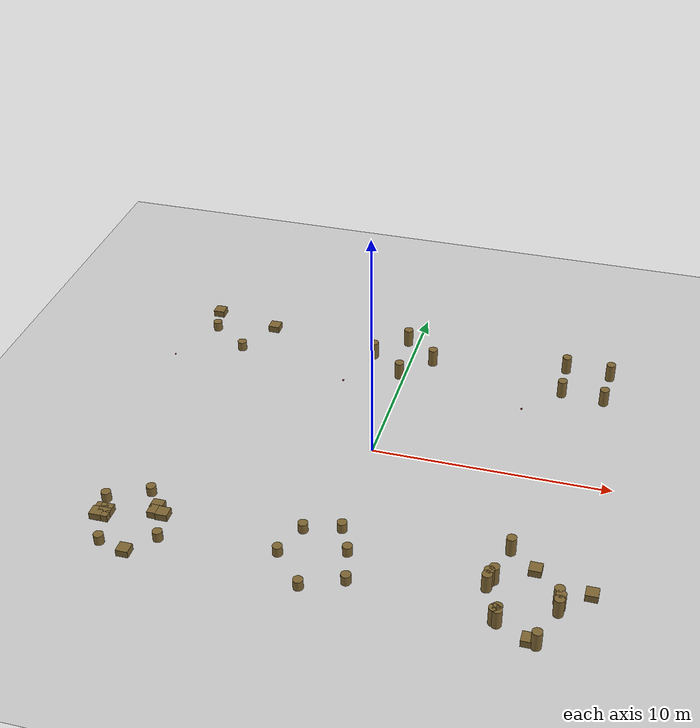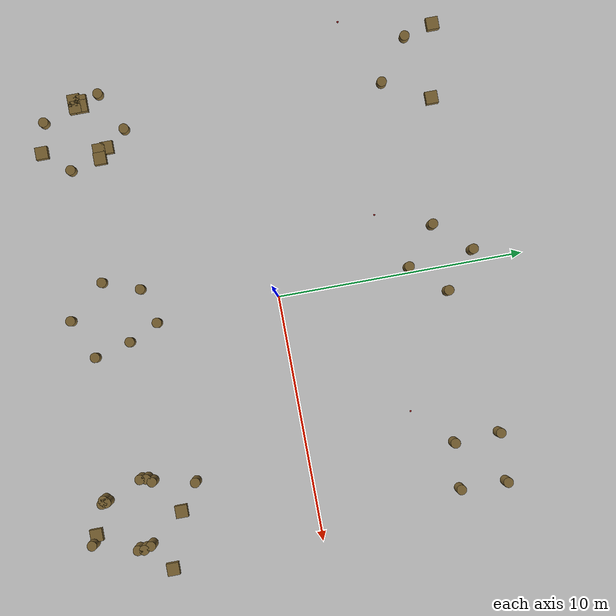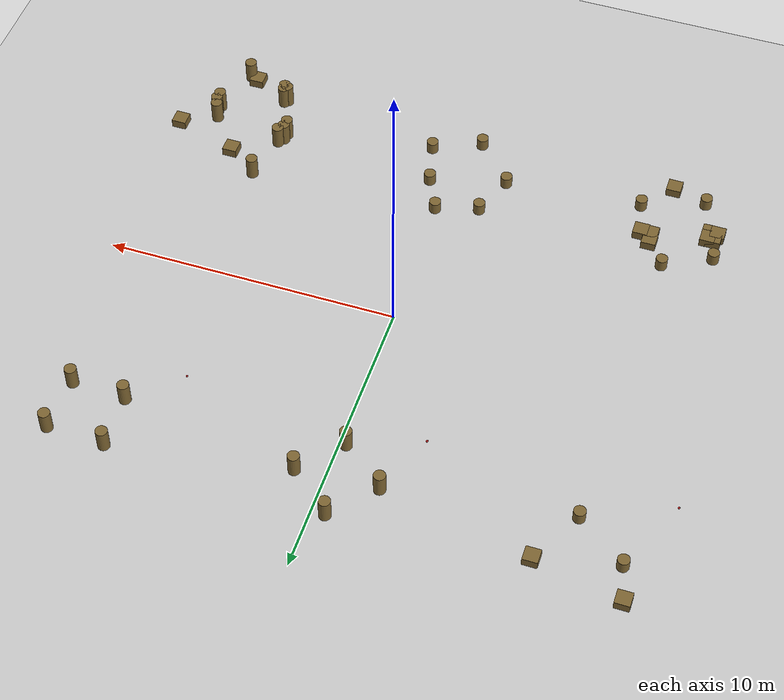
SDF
<sdf version="1.6">
 <world name="default">
  <scene><ambient>0.4 0.4 0.4 1</ambient><background>0.7 0.7 0.7 1</background><shadows>1</shadows></scene>
  <light name="sun" type="directional">
   <pose>0 0 10 0 -0 0</pose>
   <diffuse>0.8 0.8 0.8 1</diffuse>
   <specular>0.2 0.2 0.2 1</specular>
   <attenuation>
    <range>1000</range>
    <constant>0.9</constant>
    <linear>0.01</linear>
    <quadratic>0.001</quadratic>
   </attenuation>
   <direction>-0.5 0.1 -0.9</direction>
  </light>
  <model name="ground_plane">
   <static>1</static>
   <link name="link">
    <collision name="collision">
     <geometry><plane><normal>0 0 1</normal><size>100 100</size></plane></geometry>
     <surface><friction><ode><mu>100</mu><mu2>50</mu2></ode></friction></surface>
    </collision>
    <visual name="visual">
     <cast_shadows>0</cast_shadows>
     <geometry><plane><normal>0 0 1</normal><size>100 100</size></plane></geometry>
     <material>
      <script><uri>file://media/materials/scripts/gazebo.material</uri><name>Gazebo/Grey</name></script>
     </material>
    </visual>
   </link>
  </model>
  <physics name="default_physics" default="0" type="ode">
   <real_time_update_rate>1000</real_time_update_rate>
   <max_step_size>0.001</max_step_size>
   <real_time_factor>1</real_time_factor>
   <ode>
    <solver>
     <type>quick</type>
     <iters>150</iters>
     <precon_iters>0</precon_iters>
     <sor>1.4</sor>
     <use_dynamic_moi_rescaling>1</use_dynamic_moi_rescaling>
    </solver>
    <constraints>
     <cfm>1e-05</cfm>
     <erp>0.2</erp>
     <contact_max_correcting_vel>2000</contact_max_correcting_vel>
     <contact_surface_layer>0.01</contact_surface_layer>
    </constraints>
   </ode>
  </physics>
  <gravity>0 0 -9.8</gravity>
  <magnetic_field>6e-06 2.3e-05 -4.2e-05</magnetic_field>
  <atmosphere type="adiabatic"/>
  <spherical_coordinates>
   <surface_model>EARTH_WGS84</surface_model>
   <latitude_deg>0</latitude_deg>
   <longitude_deg>0</longitude_deg>
   <elevation>0</elevation>
   <heading_deg>0</heading_deg>
  </spherical_coordinates>
  <audio><device>default</device></audio>
  <model name="mini_cylinder_0_clone_0">
   <link name="link">
    <inertial>
     <mass>1</mass>
     <inertia><ixx>0.145833</ixx><ixy>0</ixy><ixz>0</ixz><iyy>0.145833</iyy><iyz>0</iyz><izz>0.125</izz></inertia>
    </inertial>
    <visual name="visual">
     <geometry><cylinder><radius>0.2</radius><length>0.8</length></cylinder></geometry>
     <material>
      <script><name>Gazebo/Grey</name><uri>file://media/materials/scripts/gazebo.material</uri></script>
      <shader type="vertex"><normal_map>__default__</normal_map></shader>
      <ambient>0.5 0.4 0.2 1</ambient>
      <diffuse>0.7 0.7 0.7 1</diffuse>
      <specular>0.01 0.01 0.01 1</specular>
      <emissive>0 0 0 1</emissive>
     </material>
    </visual>
    <collision name="collision">
     <geometry><cylinder><radius>0.2</radius><length>0.8</length></cylinder></geometry>
     <surface>
      <friction>
       <ode><mu>1</mu><mu2>1</mu2><fdir1>0 0 0</fdir1><slip1>0</slip1><slip2>0</slip2></ode>
       <torsional>
        <coefficient>1</coefficient>
        <patch_radius>0</patch_radius>
        <surface_radius>0</surface_radius>
        <use_patch_radius>1</use_patch_radius>
        <ode><slip>0</slip></ode>
       </torsional>
      </friction>
      <bounce><restitution_coefficient>0</restitution_coefficient><threshold>1e+06</threshold></bounce>
      <contact>
       <collide_without_contact>0</collide_without_contact>
       <collide_without_contact_bitmask>1</collide_without_contact_bitmask>
       <collide_bitmask>1</collide_bitmask>
       <ode>
        <soft_cfm>0</soft_cfm>
        <soft_erp>0.2</soft_erp>
        <kp>1e+13</kp>
        <kd>1</kd>
        <max_vel>0.01</max_vel>
        <min_depth>0</min_depth>
       </ode>
       <bullet>
        <split_impulse>1</split_impulse>
        <split_impulse_penetration_threshold>-0.01</split_impulse_penetration_threshold>
        <soft_cfm>0</soft_cfm>
        <soft_erp>0.2</soft_erp>
        <kp>1e+13</kp>
        <kd>1</kd>
       </bullet>
      </contact>
     </surface>
    </collision>
   </link>
   <static>1</static>
   <pose>8.88945 5.77982 0.348185 0 -0 0</pose>
  </model>
  <model name="target_0">
   <link name="link">
    <pose>0 0 0.0375 0 -0 0</pose>
    <inertial>
     <mass>0.1467</mass>
     <inertia>
      <ixx>8.25187e-05</ixx>
      <ixy>0</ixy>
      <ixz>0</ixz>
      <iyy>8.25187e-05</iyy>
      <iyz>0</iyz>
      <izz>8.25187e-05</izz>
     </inertia>
    </inertial>
    <velocity_decay><linear>0</linear><angular>0.005</angular></velocity_decay>
    <visual name="visual">
     <geometry><sphere><radius>0.0375</radius></sphere></geometry>
     <material>
      <script><uri>file://media/materials/scripts/gazebo.material</uri><name>Gazebo/Red</name></script>
      <shader type="pixel"/>
     </material>
    </visual>
    <collision name="collision">
     <geometry><sphere><radius>0.0375</radius></sphere></geometry>
     <surface>
      <friction>
       <ode><mu>1</mu><mu2>1</mu2><fdir1>0 0 0</fdir1><slip1>0</slip1><slip2>0</slip2></ode>
       <torsional>
        <coefficient>1</coefficient>
        <patch_radius>0</patch_radius>
        <surface_radius>0.01</surface_radius>
        <use_patch_radius>0</use_patch_radius>
        <ode><slip>0</slip></ode>
       </torsional>
      </friction>
      <bounce><restitution_coefficient>0</restitution_coefficient><threshold>1e+06</threshold></bounce>
      <contact>
       <collide_without_contact>0</collide_without_contact>
       <collide_without_contact_bitmask>1</collide_without_contact_bitmask>
       <collide_bitmask>1</collide_bitmask>
       <ode>
        <soft_cfm>0</soft_cfm>
        <soft_erp>0.2</soft_erp>
        <kp>100000</kp>
        <kd>100</kd>
        <max_vel>100</max_vel>
        <min_depth>0.001</min_depth>
       </ode>
       <bullet>
        <split_impulse>1</split_impulse>
        <split_impulse_penetration_threshold>-0.01</split_impulse_penetration_threshold>
        <soft_cfm>0</soft_cfm>
        <soft_erp>0.2</soft_erp>
        <kp>100000</kp>
        <kd>100</kd>
       </bullet>
      </contact>
     </surface>
    </collision>
   </link>
   <static>0</static>
   <pose>5.5098 4.40714 -0.001014 0 -0 0</pose>
  </model>
  <model name="target_1">
   <link name="link">
    <pose>0 0 0.0375 0 -0 0</pose>
    <inertial>
     <mass>0.1467</mass>
     <inertia>
      <ixx>8.25187e-05</ixx>
      <ixy>0</ixy>
      <ixz>0</ixz>
      <iyy>8.25187e-05</iyy>
      <iyz>0</iyz>
      <izz>8.25187e-05</izz>
     </inertia>
    </inertial>
    <velocity_decay><linear>0</linear><angular>0.005</angular></velocity_decay>
    <visual name="visual">
     <geometry><sphere><radius>0.0375</radius></sphere></geometry>
     <material>
      <script><uri>file://media/materials/scripts/gazebo.material</uri><name>Gazebo/Red</name></script>
      <shader type="pixel"/>
     </material>
    </visual>
    <collision name="collision">
     <geometry><sphere><radius>0.0375</radius></sphere></geometry>
     <surface>
      <friction>
       <ode><mu>1</mu><mu2>1</mu2><fdir1>0 0 0</fdir1><slip1>0</slip1><slip2>0</slip2></ode>
       <torsional>
        <coefficient>1</coefficient>
        <patch_radius>0</patch_radius>
        <surface_radius>0.01</surface_radius>
        <use_patch_radius>0</use_patch_radius>
        <ode><slip>0</slip></ode>
       </torsional>
      </friction>
      <bounce><restitution_coefficient>0</restitution_coefficient><threshold>1e+06</threshold></bounce>
      <contact>
       <collide_without_contact>0</collide_without_contact>
       <collide_without_contact_bitmask>1</collide_without_contact_bitmask>
       <collide_bitmask>1</collide_bitmask>
       <ode>
        <soft_cfm>0</soft_cfm>
        <soft_erp>0.2</soft_erp>
        <kp>100000</kp>
        <kd>100</kd>
        <max_vel>100</max_vel>
        <min_depth>0.001</min_depth>
       </ode>
       <bullet>
        <split_impulse>1</split_impulse>
        <split_impulse_penetration_threshold>-0.01</split_impulse_penetration_threshold>
        <soft_cfm>0</soft_cfm>
        <soft_erp>0.2</soft_erp>
        <kp>100000</kp>
        <kd>100</kd>
       </bullet>
      </contact>
     </surface>
    </collision>
   </link>
   <static>0</static>
   <pose>-2.56757 4.41406 -0.001014 0 -0 0</pose>
  </model>
  <model name="target_2">
   <link name="link">
    <pose>0 0 0.0375 0 -0 0</pose>
    <inertial>
     <mass>0.1467</mass>
     <inertia>
      <ixx>8.25187e-05</ixx>
      <ixy>0</ixy>
      <ixz>0</ixz>
      <iyy>8.25187e-05</iyy>
      <iyz>0</iyz>
      <izz>8.25187e-05</izz>
     </inertia>
    </inertial>
    <velocity_decay><linear>0</linear><angular>0.005</angular></velocity_decay>
    <visual name="visual">
     <geometry><sphere><radius>0.0375</radius></sphere></geometry>
     <material>
      <script><uri>file://media/materials/scripts/gazebo.material</uri><name>Gazebo/Red</name></script>
      <shader type="pixel"/>
     </material>
    </visual>
    <collision name="collision">
     <geometry><sphere><radius>0.0375</radius></sphere></geometry>
     <surface>
      <friction>
       <ode><mu>1</mu><mu2>1</mu2><fdir1>0 0 0</fdir1><slip1>0</slip1><slip2>0</slip2></ode>
       <torsional>
        <coefficient>1</coefficient>
        <patch_radius>0</patch_radius>
        <surface_radius>0.01</surface_radius>
        <use_patch_radius>0</use_patch_radius>
        <ode><slip>0</slip></ode>
       </torsional>
      </friction>
      <bounce><restitution_coefficient>0</restitution_coefficient><threshold>1e+06</threshold></bounce>
      <contact>
       <collide_without_contact>0</collide_without_contact>
       <collide_without_contact_bitmask>1</collide_without_contact_bitmask>
       <collide_bitmask>1</collide_bitmask>
       <ode>
        <soft_cfm>0</soft_cfm>
        <soft_erp>0.2</soft_erp>
        <kp>100000</kp>
        <kd>100</kd>
        <max_vel>100</max_vel>
        <min_depth>0.001</min_depth>
       </ode>
       <bullet>
        <split_impulse>1</split_impulse>
        <split_impulse_penetration_threshold>-0.01</split_impulse_penetration_threshold>
        <soft_cfm>0</soft_cfm>
        <soft_erp>0.2</soft_erp>
        <kp>100000</kp>
        <kd>100</kd>
       </bullet>
      </contact>
     </surface>
    </collision>
   </link>
   <static>0</static>
   <pose>-10.6016 4.37211 -0.001014 0 -0 0</pose>
  </model>
  <model name="mini_cylinder_0_clone_0_clone">
   <link name="link">
    <inertial>
     <mass>1</mass>
     <inertia><ixx>0.145833</ixx><ixy>0</ixy><ixz>0</ixz><iyy>0.145833</iyy><iyz>0</iyz><izz>0.125</izz></inertia>
    </inertial>
    <visual name="visual">
     <geometry><cylinder><radius>0.2</radius><length>0.8</length></cylinder></geometry>
     <material>
      <script><name>Gazebo/Grey</name><uri>file://media/materials/scripts/gazebo.material</uri></script>
      <shader type="vertex"><normal_map>__default__</normal_map></shader>
      <ambient>0.5 0.4 0.2 1</ambient>
      <diffuse>0.7 0.7 0.7 1</diffuse>
      <specular>0.01 0.01 0.01 1</specular>
      <emissive>0 0 0 1</emissive>
     </material>
    </visual>
    <collision name="collision">
     <geometry><cylinder><radius>0.2</radius><length>0.8</length></cylinder></geometry>
     <surface>
      <friction>
       <ode><mu>1</mu><mu2>1</mu2><fdir1>0 0 0</fdir1><slip1>0</slip1><slip2>0</slip2></ode>
       <torsional>
        <coefficient>1</coefficient>
        <patch_radius>0</patch_radius>
        <surface_radius>0</surface_radius>
        <use_patch_radius>1</use_patch_radius>
        <ode><slip>0</slip></ode>
       </torsional>
      </friction>
      <bounce><restitution_coefficient>0</restitution_coefficient><threshold>1e+06</threshold></bounce>
      <contact>
       <collide_without_contact>0</collide_without_contact>
       <collide_without_contact_bitmask>1</collide_without_contact_bitmask>
       <collide_bitmask>1</collide_bitmask>
       <ode>
        <soft_cfm>0</soft_cfm>
        <soft_erp>0.2</soft_erp>
        <kp>1e+13</kp>
        <kd>1</kd>
        <max_vel>0.01</max_vel>
        <min_depth>0</min_depth>
       </ode>
       <bullet>
        <split_impulse>1</split_impulse>
        <split_impulse_penetration_threshold>-0.01</split_impulse_penetration_threshold>
        <soft_cfm>0</soft_cfm>
        <soft_erp>0.2</soft_erp>
        <kp>1e+13</kp>
        <kd>1</kd>
       </bullet>
      </contact>
     </surface>
    </collision>
   </link>
   <static>1</static>
   <pose>7.02966 5.87996 0.4 0 -0 0</pose>
  </model>
  <model name="mini_cylinder_0_clone_0_clone_0">
   <link name="link">
    <inertial>
     <mass>1</mass>
     <inertia><ixx>0.145833</ixx><ixy>0</ixy><ixz>0</ixz><iyy>0.145833</iyy><iyz>0</iyz><izz>0.125</izz></inertia>
    </inertial>
    <visual name="visual">
     <geometry><cylinder><radius>0.2</radius><length>0.8</length></cylinder></geometry>
     <material>
      <script><name>Gazebo/Grey</name><uri>file://media/materials/scripts/gazebo.material</uri></script>
      <shader type="vertex"><normal_map>__default__</normal_map></shader>
      <ambient>0.5 0.4 0.2 1</ambient>
      <diffuse>0.7 0.7 0.7 1</diffuse>
      <specular>0.01 0.01 0.01 1</specular>
      <emissive>0 0 0 1</emissive>
     </material>
    </visual>
    <collision name="collision">
     <geometry><cylinder><radius>0.2</radius><length>0.8</length></cylinder></geometry>
     <surface>
      <friction>
       <ode><mu>1</mu><mu2>1</mu2><fdir1>0 0 0</fdir1><slip1>0</slip1><slip2>0</slip2></ode>
       <torsional>
        <coefficient>1</coefficient>
        <patch_radius>0</patch_radius>
        <surface_radius>0</surface_radius>
        <use_patch_radius>1</use_patch_radius>
        <ode><slip>0</slip></ode>
       </torsional>
      </friction>
      <bounce><restitution_coefficient>0</restitution_coefficient><threshold>1e+06</threshold></bounce>
      <contact>
       <collide_without_contact>0</collide_without_contact>
       <collide_without_contact_bitmask>1</collide_without_contact_bitmask>
       <collide_bitmask>1</collide_bitmask>
       <ode>
        <soft_cfm>0</soft_cfm>
        <soft_erp>0.2</soft_erp>
        <kp>1e+13</kp>
        <kd>1</kd>
        <max_vel>0.01</max_vel>
        <min_depth>0</min_depth>
       </ode>
       <bullet>
        <split_impulse>1</split_impulse>
        <split_impulse_penetration_threshold>-0.01</split_impulse_penetration_threshold>
        <soft_cfm>0</soft_cfm>
        <soft_erp>0.2</soft_erp>
        <kp>1e+13</kp>
        <kd>1</kd>
       </bullet>
      </contact>
     </surface>
    </collision>
   </link>
   <static>1</static>
   <pose>6.95356 7.73119 0.4 0 -0 0</pose>
  </model>
  <model name="mini_cylinder_0_clone_0_clone_1">
   <link name="link">
    <inertial>
     <mass>1</mass>
     <inertia><ixx>0.145833</ixx><ixy>0</ixy><ixz>0</ixz><iyy>0.145833</iyy><iyz>0</iyz><izz>0.125</izz></inertia>
    </inertial>
    <visual name="visual">
     <geometry><cylinder><radius>0.2</radius><length>0.8</length></cylinder></geometry>
     <material>
      <script><name>Gazebo/Grey</name><uri>file://media/materials/scripts/gazebo.material</uri></script>
      <shader type="vertex"><normal_map>__default__</normal_map></shader>
      <ambient>0.5 0.4 0.2 1</ambient>
      <diffuse>0.7 0.7 0.7 1</diffuse>
      <specular>0.01 0.01 0.01 1</specular>
      <emissive>0 0 0 1</emissive>
     </material>
    </visual>
    <collision name="collision">
     <geometry><cylinder><radius>0.2</radius><length>0.8</length></cylinder></geometry>
     <surface>
      <friction>
       <ode><mu>1</mu><mu2>1</mu2><fdir1>0 0 0</fdir1><slip1>0</slip1><slip2>0</slip2></ode>
       <torsional>
        <coefficient>1</coefficient>
        <patch_radius>0</patch_radius>
        <surface_radius>0</surface_radius>
        <use_patch_radius>1</use_patch_radius>
        <ode><slip>0</slip></ode>
       </torsional>
      </friction>
      <bounce><restitution_coefficient>0</restitution_coefficient><threshold>1e+06</threshold></bounce>
      <contact>
       <collide_without_contact>0</collide_without_contact>
       <collide_without_contact_bitmask>1</collide_without_contact_bitmask>
       <collide_bitmask>1</collide_bitmask>
       <ode>
        <soft_cfm>0</soft_cfm>
        <soft_erp>0.2</soft_erp>
        <kp>1e+13</kp>
        <kd>1</kd>
        <max_vel>0.01</max_vel>
        <min_depth>0</min_depth>
       </ode>
       <bullet>
        <split_impulse>1</split_impulse>
        <split_impulse_penetration_threshold>-0.01</split_impulse_penetration_threshold>
        <soft_cfm>0</soft_cfm>
        <soft_erp>0.2</soft_erp>
        <kp>1e+13</kp>
        <kd>1</kd>
       </bullet>
      </contact>
     </surface>
    </collision>
   </link>
   <static>1</static>
   <pose>8.93133 7.65541 0.4 0 -0 0</pose>
  </model>
  <model name="mini_cylinder_0_clone_0_clone_2">
   <link name="link">
    <inertial>
     <mass>1</mass>
     <inertia><ixx>0.145833</ixx><ixy>0</ixy><ixz>0</ixz><iyy>0.145833</iyy><iyz>0</iyz><izz>0.125</izz></inertia>
    </inertial>
    <visual name="visual">
     <geometry><cylinder><radius>0.2</radius><length>0.8</length></cylinder></geometry>
     <material>
      <script><name>Gazebo/Grey</name><uri>file://media/materials/scripts/gazebo.material</uri></script>
      <shader type="vertex"><normal_map>__default__</normal_map></shader>
      <ambient>0.5 0.4 0.2 1</ambient>
      <diffuse>0.7 0.7 0.7 1</diffuse>
      <specular>0.01 0.01 0.01 1</specular>
      <emissive>0 0 0 1</emissive>
     </material>
    </visual>
    <collision name="collision">
     <geometry><cylinder><radius>0.2</radius><length>0.8</length></cylinder></geometry>
     <surface>
      <friction>
       <ode><mu>1</mu><mu2>1</mu2><fdir1>0 0 0</fdir1><slip1>0</slip1><slip2>0</slip2></ode>
       <torsional>
        <coefficient>1</coefficient>
        <patch_radius>0</patch_radius>
        <surface_radius>0</surface_radius>
        <use_patch_radius>1</use_patch_radius>
        <ode><slip>0</slip></ode>
       </torsional>
      </friction>
      <bounce><restitution_coefficient>0</restitution_coefficient><threshold>1e+06</threshold></bounce>
      <contact>
       <collide_without_contact>0</collide_without_contact>
       <collide_without_contact_bitmask>1</collide_without_contact_bitmask>
       <collide_bitmask>1</collide_bitmask>
       <ode>
        <soft_cfm>0</soft_cfm>
        <soft_erp>0.2</soft_erp>
        <kp>1e+13</kp>
        <kd>1</kd>
        <max_vel>0.01</max_vel>
        <min_depth>0</min_depth>
       </ode>
       <bullet>
        <split_impulse>1</split_impulse>
        <split_impulse_penetration_threshold>-0.01</split_impulse_penetration_threshold>
        <soft_cfm>0</soft_cfm>
        <soft_erp>0.2</soft_erp>
        <kp>1e+13</kp>
        <kd>1</kd>
       </bullet>
      </contact>
     </surface>
    </collision>
   </link>
   <static>1</static>
   <pose>8.85526 -6.7474 0.4 0 -0 0</pose>
  </model>
  <model name="mini_cylinder_0_clone_0_clone_5">
   <link name="link">
    <inertial>
     <mass>1</mass>
     <inertia><ixx>0.145833</ixx><ixy>0</ixy><ixz>0</ixz><iyy>0.145833</iyy><iyz>0</iyz><izz>0.125</izz></inertia>
    </inertial>
    <visual name="visual">
     <geometry><cylinder><radius>0.2</radius><length>0.8</length></cylinder></geometry>
     <material>
      <script><name>Gazebo/Grey</name><uri>file://media/materials/scripts/gazebo.material</uri></script>
      <shader type="vertex"><normal_map>__default__</normal_map></shader>
      <ambient>0.5 0.4 0.2 1</ambient>
      <diffuse>0.7 0.7 0.7 1</diffuse>
      <specular>0.01 0.01 0.01 1</specular>
      <emissive>0 0 0 1</emissive>
     </material>
    </visual>
    <collision name="collision">
     <geometry><cylinder><radius>0.2</radius><length>0.8</length></cylinder></geometry>
     <surface>
      <friction>
       <ode><mu>1</mu><mu2>1</mu2><fdir1>0 0 0</fdir1><slip1>0</slip1><slip2>0</slip2></ode>
       <torsional>
        <coefficient>1</coefficient>
        <patch_radius>0</patch_radius>
        <surface_radius>0</surface_radius>
        <use_patch_radius>1</use_patch_radius>
        <ode><slip>0</slip></ode>
       </torsional>
      </friction>
      <bounce><restitution_coefficient>0</restitution_coefficient><threshold>1e+06</threshold></bounce>
      <contact>
       <collide_without_contact>0</collide_without_contact>
       <collide_without_contact_bitmask>1</collide_without_contact_bitmask>
       <collide_bitmask>1</collide_bitmask>
       <ode>
        <soft_cfm>0</soft_cfm>
        <soft_erp>0.2</soft_erp>
        <kp>1e+13</kp>
        <kd>1</kd>
        <max_vel>0.01</max_vel>
        <min_depth>0</min_depth>
       </ode>
       <bullet>
        <split_impulse>1</split_impulse>
        <split_impulse_penetration_threshold>-0.01</split_impulse_penetration_threshold>
        <soft_cfm>0</soft_cfm>
        <soft_erp>0.2</soft_erp>
        <kp>1e+13</kp>
        <kd>1</kd>
       </bullet>
      </contact>
     </surface>
    </collision>
   </link>
   <static>1</static>
   <pose>8.9567 -7.0263 0.4 0 -0 0</pose>
  </model>
  <model name="mini_cylinder_0_clone_0_clone_6">
   <link name="link">
    <inertial>
     <mass>1</mass>
     <inertia><ixx>0.145833</ixx><ixy>0</ixy><ixz>0</ixz><iyy>0.145833</iyy><iyz>0</iyz><izz>0.125</izz></inertia>
    </inertial>
    <visual name="visual">
     <geometry><cylinder><radius>0.2</radius><length>0.8</length></cylinder></geometry>
     <material>
      <script><name>Gazebo/Grey</name><uri>file://media/materials/scripts/gazebo.material</uri></script>
      <shader type="vertex"><normal_map>__default__</normal_map></shader>
      <ambient>0.5 0.4 0.2 1</ambient>
      <diffuse>0.7 0.7 0.7 1</diffuse>
      <specular>0.01 0.01 0.01 1</specular>
      <emissive>0 0 0 1</emissive>
     </material>
    </visual>
    <collision name="collision">
     <geometry><cylinder><radius>0.2</radius><length>0.8</length></cylinder></geometry>
     <surface>
      <friction>
       <ode><mu>1</mu><mu2>1</mu2><fdir1>0 0 0</fdir1><slip1>0</slip1><slip2>0</slip2></ode>
       <torsional>
        <coefficient>1</coefficient>
        <patch_radius>0</patch_radius>
        <surface_radius>0</surface_radius>
        <use_patch_radius>1</use_patch_radius>
        <ode><slip>0</slip></ode>
       </torsional>
      </friction>
      <bounce><restitution_coefficient>0</restitution_coefficient><threshold>1e+06</threshold></bounce>
      <contact>
       <collide_without_contact>0</collide_without_contact>
       <collide_without_contact_bitmask>1</collide_without_contact_bitmask>
       <collide_bitmask>1</collide_bitmask>
       <ode>
        <soft_cfm>0</soft_cfm>
        <soft_erp>0.2</soft_erp>
        <kp>1e+13</kp>
        <kd>1</kd>
        <max_vel>0.01</max_vel>
        <min_depth>0</min_depth>
       </ode>
       <bullet>
        <split_impulse>1</split_impulse>
        <split_impulse_penetration_threshold>-0.01</split_impulse_penetration_threshold>
        <soft_cfm>0</soft_cfm>
        <soft_erp>0.2</soft_erp>
        <kp>1e+13</kp>
        <kd>1</kd>
       </bullet>
      </contact>
     </surface>
    </collision>
   </link>
   <static>1</static>
   <pose>8.93133 -7.27982 0.4 0 -0 0</pose>
  </model>
  <model name="mini_cylinder_0_clone_0_clone_7">
   <link name="link">
    <inertial>
     <mass>1</mass>
     <inertia><ixx>0.145833</ixx><ixy>0</ixy><ixz>0</ixz><iyy>0.145833</iyy><iyz>0</iyz><izz>0.125</izz></inertia>
    </inertial>
    <visual name="visual">
     <geometry><cylinder><radius>0.2</radius><length>0.8</length></cylinder></geometry>
     <material>
      <script><name>Gazebo/Grey</name><uri>file://media/materials/scripts/gazebo.material</uri></script>
      <shader type="vertex"><normal_map>__default__</normal_map></shader>
      <ambient>0.5 0.4 0.2 1</ambient>
      <diffuse>0.7 0.7 0.7 1</diffuse>
      <specular>0.01 0.01 0.01 1</specular>
      <emissive>0 0 0 1</emissive>
     </material>
    </visual>
    <collision name="collision">
     <geometry><cylinder><radius>0.2</radius><length>0.8</length></cylinder></geometry>
     <surface>
      <friction>
       <ode><mu>1</mu><mu2>1</mu2><fdir1>0 0 0</fdir1><slip1>0</slip1><slip2>0</slip2></ode>
       <torsional>
        <coefficient>1</coefficient>
        <patch_radius>0</patch_radius>
        <surface_radius>0</surface_radius>
        <use_patch_radius>1</use_patch_radius>
        <ode><slip>0</slip></ode>
       </torsional>
      </friction>
      <bounce><restitution_coefficient>0</restitution_coefficient><threshold>1e+06</threshold></bounce>
      <contact>
       <collide_without_contact>0</collide_without_contact>
       <collide_without_contact_bitmask>1</collide_without_contact_bitmask>
       <collide_bitmask>1</collide_bitmask>
       <ode>
        <soft_cfm>0</soft_cfm>
        <soft_erp>0.2</soft_erp>
        <kp>1e+13</kp>
        <kd>1</kd>
        <max_vel>0.01</max_vel>
        <min_depth>0</min_depth>
       </ode>
       <bullet>
        <split_impulse>1</split_impulse>
        <split_impulse_penetration_threshold>-0.01</split_impulse_penetration_threshold>
        <soft_cfm>0</soft_cfm>
        <soft_erp>0.2</soft_erp>
        <kp>1e+13</kp>
        <kd>1</kd>
       </bullet>
      </contact>
     </surface>
    </collision>
   </link>
   <static>1</static>
   <pose>6.87749 -8.36985 0.4 0 -0 0</pose>
  </model>
  <model name="mini_cylinder_0_clone_0_clone_8">
   <link name="link">
    <inertial>
     <mass>1</mass>
     <inertia><ixx>0.145833</ixx><ixy>0</ixy><ixz>0</ixz><iyy>0.145833</iyy><iyz>0</iyz><izz>0.125</izz></inertia>
    </inertial>
    <visual name="visual">
     <geometry><cylinder><radius>0.2</radius><length>0.8</length></cylinder></geometry>
     <material>
      <script><name>Gazebo/Grey</name><uri>file://media/materials/scripts/gazebo.material</uri></script>
      <shader type="vertex"><normal_map>__default__</normal_map></shader>
      <ambient>0.5 0.4 0.2 1</ambient>
      <diffuse>0.7 0.7 0.7 1</diffuse>
      <specular>0.01 0.01 0.01 1</specular>
      <emissive>0 0 0 1</emissive>
     </material>
    </visual>
    <collision name="collision">
     <geometry><cylinder><radius>0.2</radius><length>0.8</length></cylinder></geometry>
     <surface>
      <friction>
       <ode><mu>1</mu><mu2>1</mu2><fdir1>0 0 0</fdir1><slip1>0</slip1><slip2>0</slip2></ode>
       <torsional>
        <coefficient>1</coefficient>
        <patch_radius>0</patch_radius>
        <surface_radius>0</surface_radius>
        <use_patch_radius>1</use_patch_radius>
        <ode><slip>0</slip></ode>
       </torsional>
      </friction>
      <bounce><restitution_coefficient>0</restitution_coefficient><threshold>1e+06</threshold></bounce>
      <contact>
       <collide_without_contact>0</collide_without_contact>
       <collide_without_contact_bitmask>1</collide_without_contact_bitmask>
       <collide_bitmask>1</collide_bitmask>
       <ode>
        <soft_cfm>0</soft_cfm>
        <soft_erp>0.2</soft_erp>
        <kp>1e+13</kp>
        <kd>1</kd>
        <max_vel>0.01</max_vel>
        <min_depth>0</min_depth>
       </ode>
       <bullet>
        <split_impulse>1</split_impulse>
        <split_impulse_penetration_threshold>-0.01</split_impulse_penetration_threshold>
        <soft_cfm>0</soft_cfm>
        <soft_erp>0.2</soft_erp>
        <kp>1e+13</kp>
        <kd>1</kd>
       </bullet>
      </contact>
     </surface>
    </collision>
   </link>
   <static>1</static>
   <pose>6.75065 -8.29407 0.4 0 -0 0</pose>
  </model>
  <model name="mini_cylinder_0_clone_0_clone_9">
   <link name="link">
    <inertial>
     <mass>1</mass>
     <inertia><ixx>0.145833</ixx><ixy>0</ixy><ixz>0</ixz><iyy>0.145833</iyy><iyz>0</iyz><izz>0.125</izz></inertia>
    </inertial>
    <visual name="visual">
     <geometry><cylinder><radius>0.2</radius><length>0.8</length></cylinder></geometry>
     <material>
      <script><name>Gazebo/Grey</name><uri>file://media/materials/scripts/gazebo.material</uri></script>
      <shader type="vertex"><normal_map>__default__</normal_map></shader>
      <ambient>0.5 0.4 0.2 1</ambient>
      <diffuse>0.7 0.7 0.7 1</diffuse>
      <specular>0.01 0.01 0.01 1</specular>
      <emissive>0 0 0 1</emissive>
     </material>
    </visual>
    <collision name="collision">
     <geometry><cylinder><radius>0.2</radius><length>0.8</length></cylinder></geometry>
     <surface>
      <friction>
       <ode><mu>1</mu><mu2>1</mu2><fdir1>0 0 0</fdir1><slip1>0</slip1><slip2>0</slip2></ode>
       <torsional>
        <coefficient>1</coefficient>
        <patch_radius>0</patch_radius>
        <surface_radius>0</surface_radius>
        <use_patch_radius>1</use_patch_radius>
        <ode><slip>0</slip></ode>
       </torsional>
      </friction>
      <bounce><restitution_coefficient>0</restitution_coefficient><threshold>1e+06</threshold></bounce>
      <contact>
       <collide_without_contact>0</collide_without_contact>
       <collide_without_contact_bitmask>1</collide_without_contact_bitmask>
       <collide_bitmask>1</collide_bitmask>
       <ode>
        <soft_cfm>0</soft_cfm>
        <soft_erp>0.2</soft_erp>
        <kp>1e+13</kp>
        <kd>1</kd>
        <max_vel>0.01</max_vel>
        <min_depth>0</min_depth>
       </ode>
       <bullet>
        <split_impulse>1</split_impulse>
        <split_impulse_penetration_threshold>-0.01</split_impulse_penetration_threshold>
        <soft_cfm>0</soft_cfm>
        <soft_erp>0.2</soft_erp>
        <kp>1e+13</kp>
        <kd>1</kd>
       </bullet>
      </contact>
     </surface>
    </collision>
   </link>
   <static>1</static>
   <pose>6.85208 -8.1926 0.4 0 -0 0</pose>
  </model>
  <model name="mini_cylinder_0_clone_0_clone_10">
   <link name="link">
    <inertial>
     <mass>1</mass>
     <inertia><ixx>0.145833</ixx><ixy>0</ixy><ixz>0</ixz><iyy>0.145833</iyy><iyz>0</iyz><izz>0.125</izz></inertia>
    </inertial>
    <visual name="visual">
     <geometry><cylinder><radius>0.2</radius><length>0.8</length></cylinder></geometry>
     <material>
      <script><name>Gazebo/Grey</name><uri>file://media/materials/scripts/gazebo.material</uri></script>
      <shader type="vertex"><normal_map>__default__</normal_map></shader>
      <ambient>0.5 0.4 0.2 1</ambient>
      <diffuse>0.7 0.7 0.7 1</diffuse>
      <specular>0.01 0.01 0.01 1</specular>
      <emissive>0 0 0 1</emissive>
     </material>
    </visual>
    <collision name="collision">
     <geometry><cylinder><radius>0.2</radius><length>0.8</length></cylinder></geometry>
     <surface>
      <friction>
       <ode><mu>1</mu><mu2>1</mu2><fdir1>0 0 0</fdir1><slip1>0</slip1><slip2>0</slip2></ode>
       <torsional>
        <coefficient>1</coefficient>
        <patch_radius>0</patch_radius>
        <surface_radius>0</surface_radius>
        <use_patch_radius>1</use_patch_radius>
        <ode><slip>0</slip></ode>
       </torsional>
      </friction>
      <bounce><restitution_coefficient>0</restitution_coefficient><threshold>1e+06</threshold></bounce>
      <contact>
       <collide_without_contact>0</collide_without_contact>
       <collide_without_contact_bitmask>1</collide_without_contact_bitmask>
       <collide_bitmask>1</collide_bitmask>
       <ode>
        <soft_cfm>0</soft_cfm>
        <soft_erp>0.2</soft_erp>
        <kp>1e+13</kp>
        <kd>1</kd>
        <max_vel>0.01</max_vel>
        <min_depth>0</min_depth>
       </ode>
       <bullet>
        <split_impulse>1</split_impulse>
        <split_impulse_penetration_threshold>-0.01</split_impulse_penetration_threshold>
        <soft_cfm>0</soft_cfm>
        <soft_erp>0.2</soft_erp>
        <kp>1e+13</kp>
        <kd>1</kd>
       </bullet>
      </contact>
     </surface>
    </collision>
   </link>
   <static>1</static>
   <pose>6.19287 -6.72187 0.4 0 -0 0</pose>
  </model>
  <model name="mini_cylinder_0_clone_0_clone_11">
   <link name="link">
    <inertial>
     <mass>1</mass>
     <inertia><ixx>0.145833</ixx><ixy>0</ixy><ixz>0</ixz><iyy>0.145833</iyy><iyz>0</iyz><izz>0.125</izz></inertia>
    </inertial>
    <visual name="visual">
     <geometry><cylinder><radius>0.2</radius><length>0.8</length></cylinder></geometry>
     <material>
      <script><name>Gazebo/Grey</name><uri>file://media/materials/scripts/gazebo.material</uri></script>
      <shader type="vertex"><normal_map>__default__</normal_map></shader>
      <ambient>0.5 0.4 0.2 1</ambient>
      <diffuse>0.7 0.7 0.7 1</diffuse>
      <specular>0.01 0.01 0.01 1</specular>
      <emissive>0 0 0 1</emissive>
     </material>
    </visual>
    <collision name="collision">
     <geometry><cylinder><radius>0.2</radius><length>0.8</length></cylinder></geometry>
     <surface>
      <friction>
       <ode><mu>1</mu><mu2>1</mu2><fdir1>0 0 0</fdir1><slip1>0</slip1><slip2>0</slip2></ode>
       <torsional>
        <coefficient>1</coefficient>
        <patch_radius>0</patch_radius>
        <surface_radius>0</surface_radius>
        <use_patch_radius>1</use_patch_radius>
        <ode><slip>0</slip></ode>
       </torsional>
      </friction>
      <bounce><restitution_coefficient>0</restitution_coefficient><threshold>1e+06</threshold></bounce>
      <contact>
       <collide_without_contact>0</collide_without_contact>
       <collide_without_contact_bitmask>1</collide_without_contact_bitmask>
       <collide_bitmask>1</collide_bitmask>
       <ode>
        <soft_cfm>0</soft_cfm>
        <soft_erp>0.2</soft_erp>
        <kp>1e+13</kp>
        <kd>1</kd>
        <max_vel>0.01</max_vel>
        <min_depth>0</min_depth>
       </ode>
       <bullet>
        <split_impulse>1</split_impulse>
        <split_impulse_penetration_threshold>-0.01</split_impulse_penetration_threshold>
        <soft_cfm>0</soft_cfm>
        <soft_erp>0.2</soft_erp>
        <kp>1e+13</kp>
        <kd>1</kd>
       </bullet>
      </contact>
     </surface>
    </collision>
   </link>
   <static>1</static>
   <pose>6.2182 -6.47155 0.4 0 -0 0</pose>
  </model>
  <model name="mini_cylinder_0_clone_0_clone_12">
   <link name="link">
    <inertial>
     <mass>1</mass>
     <inertia><ixx>0.145833</ixx><ixy>0</ixy><ixz>0</ixz><iyy>0.145833</iyy><iyz>0</iyz><izz>0.125</izz></inertia>
    </inertial>
    <visual name="visual">
     <geometry><cylinder><radius>0.2</radius><length>0.8</length></cylinder></geometry>
     <material>
      <script><name>Gazebo/Grey</name><uri>file://media/materials/scripts/gazebo.material</uri></script>
      <shader type="vertex"><normal_map>__default__</normal_map></shader>
      <ambient>0.5 0.4 0.2 1</ambient>
      <diffuse>0.7 0.7 0.7 1</diffuse>
      <specular>0.01 0.01 0.01 1</specular>
      <emissive>0 0 0 1</emissive>
     </material>
    </visual>
    <collision name="collision">
     <geometry><cylinder><radius>0.2</radius><length>0.8</length></cylinder></geometry>
     <surface>
      <friction>
       <ode><mu>1</mu><mu2>1</mu2><fdir1>0 0 0</fdir1><slip1>0</slip1><slip2>0</slip2></ode>
       <torsional>
        <coefficient>1</coefficient>
        <patch_radius>0</patch_radius>
        <surface_radius>0</surface_radius>
        <use_patch_radius>1</use_patch_radius>
        <ode><slip>0</slip></ode>
       </torsional>
      </friction>
      <bounce><restitution_coefficient>0</restitution_coefficient><threshold>1e+06</threshold></bounce>
      <contact>
       <collide_without_contact>0</collide_without_contact>
       <collide_without_contact_bitmask>1</collide_without_contact_bitmask>
       <collide_bitmask>1</collide_bitmask>
       <ode>
        <soft_cfm>0</soft_cfm>
        <soft_erp>0.2</soft_erp>
        <kp>1e+13</kp>
        <kd>1</kd>
        <max_vel>0.01</max_vel>
        <min_depth>0</min_depth>
       </ode>
       <bullet>
        <split_impulse>1</split_impulse>
        <split_impulse_penetration_threshold>-0.01</split_impulse_penetration_threshold>
        <soft_cfm>0</soft_cfm>
        <soft_erp>0.2</soft_erp>
        <kp>1e+13</kp>
        <kd>1</kd>
       </bullet>
      </contact>
     </surface>
    </collision>
   </link>
   <static>1</static>
   <pose>6.37037 -6.26877 0.4 0 -0 0</pose>
  </model>
  <model name="mini_box_clone_clone_3_clone">
   <link name="link">
    <inertial>
     <mass>1</mass>
     <inertia>
      <ixx>0.166667</ixx>
      <ixy>0</ixy>
      <ixz>0</ixz>
      <iyy>0.166667</iyy>
      <iyz>0</iyz>
      <izz>0.166667</izz>
     </inertia>
    </inertial>
    <visual name="visual">
     <geometry><box><size>0.5 0.5 0.3</size></box></geometry>
     <material>
      <script><name>Gazebo/Grey</name><uri>file://media/materials/scripts/gazebo.material</uri></script>
      <shader type="vertex"><normal_map>__default__</normal_map></shader>
      <ambient>0.5 0.4 0.2 1</ambient>
      <diffuse>0.7 0.7 0.7 1</diffuse>
      <specular>0.01 0.01 0.01 1</specular>
      <emissive>0 0 0 1</emissive>
     </material>
    </visual>
    <collision name="collision">
     <geometry><box><size>0.5 0.5 0.3</size></box></geometry>
     <surface>
      <friction>
       <ode><mu>1</mu><mu2>1</mu2><fdir1>0 0 0</fdir1><slip1>0</slip1><slip2>0</slip2></ode>
       <torsional>
        <coefficient>1</coefficient>
        <patch_radius>0</patch_radius>
        <surface_radius>0</surface_radius>
        <use_patch_radius>1</use_patch_radius>
        <ode><slip>0</slip></ode>
       </torsional>
      </friction>
      <bounce><restitution_coefficient>0</restitution_coefficient><threshold>1e+06</threshold></bounce>
      <contact>
       <collide_without_contact>0</collide_without_contact>
       <collide_without_contact_bitmask>1</collide_without_contact_bitmask>
       <collide_bitmask>1</collide_bitmask>
       <ode>
        <soft_cfm>0</soft_cfm>
        <soft_erp>0.2</soft_erp>
        <kp>1e+13</kp>
        <kd>1</kd>
        <max_vel>0.01</max_vel>
        <min_depth>0</min_depth>
       </ode>
       <bullet>
        <split_impulse>1</split_impulse>
        <split_impulse_penetration_threshold>-0.01</split_impulse_penetration_threshold>
        <soft_cfm>0</soft_cfm>
        <soft_erp>0.2</soft_erp>
        <kp>1e+13</kp>
        <kd>1</kd>
       </bullet>
      </contact>
     </surface>
    </collision>
   </link>
   <static>1</static>
   <pose>7.79044 -5.38056 0.15 0 -0 0</pose>
  </model>
  <model name="mini_box_clone_clone_3_clone_0">
   <link name="link">
    <inertial>
     <mass>1</mass>
     <inertia>
      <ixx>0.166667</ixx>
      <ixy>0</ixy>
      <ixz>0</ixz>
      <iyy>0.166667</iyy>
      <iyz>0</iyz>
      <izz>0.166667</izz>
     </inertia>
    </inertial>
    <visual name="visual">
     <geometry><box><size>0.5 0.5 0.3</size></box></geometry>
     <material>
      <script><name>Gazebo/Grey</name><uri>file://media/materials/scripts/gazebo.material</uri></script>
      <shader type="vertex"><normal_map>__default__</normal_map></shader>
      <ambient>0.5 0.4 0.2 1</ambient>
      <diffuse>0.7 0.7 0.7 1</diffuse>
      <specular>0.01 0.01 0.01 1</specular>
      <emissive>0 0 0 1</emissive>
     </material>
    </visual>
    <collision name="collision">
     <geometry><box><size>0.5 0.5 0.3</size></box></geometry>
     <surface>
      <friction>
       <ode><mu>1</mu><mu2>1</mu2><fdir1>0 0 0</fdir1><slip1>0</slip1><slip2>0</slip2></ode>
       <torsional>
        <coefficient>1</coefficient>
        <patch_radius>0</patch_radius>
        <surface_radius>0</surface_radius>
        <use_patch_radius>1</use_patch_radius>
        <ode><slip>0</slip></ode>
       </torsional>
      </friction>
      <bounce><restitution_coefficient>0</restitution_coefficient><threshold>1e+06</threshold></bounce>
      <contact>
       <collide_without_contact>0</collide_without_contact>
       <collide_without_contact_bitmask>1</collide_without_contact_bitmask>
       <collide_bitmask>1</collide_bitmask>
       <ode>
        <soft_cfm>0</soft_cfm>
        <soft_erp>0.2</soft_erp>
        <kp>1e+13</kp>
        <kd>1</kd>
        <max_vel>0.01</max_vel>
        <min_depth>0</min_depth>
       </ode>
       <bullet>
        <split_impulse>1</split_impulse>
        <split_impulse_penetration_threshold>-0.01</split_impulse_penetration_threshold>
        <soft_cfm>0</soft_cfm>
        <soft_erp>0.2</soft_erp>
        <kp>1e+13</kp>
        <kd>1</kd>
       </bullet>
      </contact>
     </surface>
    </collision>
   </link>
   <static>1</static>
   <pose>8.12011 -8.90516 0.15 0 -0 0</pose>
  </model>
  <model name="mini_box_clone_clone_3_clone_1">
   <link name="link">
    <inertial>
     <mass>1</mass>
     <inertia>
      <ixx>0.166667</ixx>
      <ixy>0</ixy>
      <ixz>0</ixz>
      <iyy>0.166667</iyy>
      <iyz>0</iyz>
      <izz>0.166667</izz>
     </inertia>
    </inertial>
    <visual name="visual">
     <geometry><box><size>0.5 0.5 0.3</size></box></geometry>
     <material>
      <script><name>Gazebo/Grey</name><uri>file://media/materials/scripts/gazebo.material</uri></script>
      <shader type="vertex"><normal_map>__default__</normal_map></shader>
      <ambient>0.5 0.4 0.2 1</ambient>
      <diffuse>0.7 0.7 0.7 1</diffuse>
      <specular>0.01 0.01 0.01 1</specular>
      <emissive>0 0 0 1</emissive>
     </material>
    </visual>
    <collision name="collision">
     <geometry><box><size>0.5 0.5 0.3</size></box></geometry>
     <surface>
      <friction>
       <ode><mu>1</mu><mu2>1</mu2><fdir1>0 0 0</fdir1><slip1>0</slip1><slip2>0</slip2></ode>
       <torsional>
        <coefficient>1</coefficient>
        <patch_radius>0</patch_radius>
        <surface_radius>0</surface_radius>
        <use_patch_radius>1</use_patch_radius>
        <ode><slip>0</slip></ode>
       </torsional>
      </friction>
      <bounce><restitution_coefficient>0</restitution_coefficient><threshold>1e+06</threshold></bounce>
      <contact>
       <collide_without_contact>0</collide_without_contact>
       <collide_without_contact_bitmask>1</collide_without_contact_bitmask>
       <collide_bitmask>1</collide_bitmask>
       <ode>
        <soft_cfm>0</soft_cfm>
        <soft_erp>0.2</soft_erp>
        <kp>1e+13</kp>
        <kd>1</kd>
        <max_vel>0.01</max_vel>
        <min_depth>0</min_depth>
       </ode>
       <bullet>
        <split_impulse>1</split_impulse>
        <split_impulse_penetration_threshold>-0.01</split_impulse_penetration_threshold>
        <soft_cfm>0</soft_cfm>
        <soft_erp>0.2</soft_erp>
        <kp>1e+13</kp>
        <kd>1</kd>
       </bullet>
      </contact>
     </surface>
    </collision>
   </link>
   <static>1</static>
   <pose>9.99645 -6.11609 0.15 0 -0 0</pose>
  </model>
  <model name="mini_cylinder_0_clone_0_clone_12_clone">
   <link name="link">
    <inertial>
     <mass>1</mass>
     <inertia><ixx>0.145833</ixx><ixy>0</ixy><ixz>0</ixz><iyy>0.145833</iyy><iyz>0</iyz><izz>0.125</izz></inertia>
    </inertial>
    <visual name="visual">
     <geometry><cylinder><radius>0.2</radius><length>0.8</length></cylinder></geometry>
     <material>
      <script><name>Gazebo/Grey</name><uri>file://media/materials/scripts/gazebo.material</uri></script>
      <shader type="vertex"><normal_map>__default__</normal_map></shader>
      <ambient>0.5 0.4 0.2 1</ambient>
      <diffuse>0.7 0.7 0.7 1</diffuse>
      <specular>0.01 0.01 0.01 1</specular>
      <emissive>0 0 0 1</emissive>
     </material>
    </visual>
    <collision name="collision">
     <geometry><cylinder><radius>0.2</radius><length>0.8</length></cylinder></geometry>
     <surface>
      <friction>
       <ode><mu>1</mu><mu2>1</mu2><fdir1>0 0 0</fdir1><slip1>0</slip1><slip2>0</slip2></ode>
       <torsional>
        <coefficient>1</coefficient>
        <patch_radius>0</patch_radius>
        <surface_radius>0</surface_radius>
        <use_patch_radius>1</use_patch_radius>
        <ode><slip>0</slip></ode>
       </torsional>
      </friction>
      <bounce><restitution_coefficient>0</restitution_coefficient><threshold>1e+06</threshold></bounce>
      <contact>
       <collide_without_contact>0</collide_without_contact>
       <collide_without_contact_bitmask>1</collide_without_contact_bitmask>
       <collide_bitmask>1</collide_bitmask>
       <ode>
        <soft_cfm>0</soft_cfm>
        <soft_erp>0.2</soft_erp>
        <kp>1e+13</kp>
        <kd>1</kd>
        <max_vel>0.01</max_vel>
        <min_depth>0</min_depth>
       </ode>
       <bullet>
        <split_impulse>1</split_impulse>
        <split_impulse_penetration_threshold>-0.01</split_impulse_penetration_threshold>
        <soft_cfm>0</soft_cfm>
        <soft_erp>0.2</soft_erp>
        <kp>1e+13</kp>
        <kd>1</kd>
       </bullet>
      </contact>
     </surface>
    </collision>
   </link>
   <static>1</static>
   <pose>6.70318 -4.57824 0.4 0 -0 0</pose>
  </model>
  <model name="mini_cylinder_0_clone_0_clone_12_clone_0">
   <link name="link">
    <inertial>
     <mass>1</mass>
     <inertia><ixx>0.145833</ixx><ixy>0</ixy><ixz>0</ixz><iyy>0.145833</iyy><iyz>0</iyz><izz>0.125</izz></inertia>
    </inertial>
    <visual name="visual">
     <geometry><cylinder><radius>0.2</radius><length>0.8</length></cylinder></geometry>
     <material>
      <script><name>Gazebo/Grey</name><uri>file://media/materials/scripts/gazebo.material</uri></script>
      <shader type="vertex"><normal_map>__default__</normal_map></shader>
      <ambient>0.5 0.4 0.2 1</ambient>
      <diffuse>0.7 0.7 0.7 1</diffuse>
      <specular>0.01 0.01 0.01 1</specular>
      <emissive>0 0 0 1</emissive>
     </material>
    </visual>
    <collision name="collision">
     <geometry><cylinder><radius>0.2</radius><length>0.8</length></cylinder></geometry>
     <surface>
      <friction>
       <ode><mu>1</mu><mu2>1</mu2><fdir1>0 0 0</fdir1><slip1>0</slip1><slip2>0</slip2></ode>
       <torsional>
        <coefficient>1</coefficient>
        <patch_radius>0</patch_radius>
        <surface_radius>0</surface_radius>
        <use_patch_radius>1</use_patch_radius>
        <ode><slip>0</slip></ode>
       </torsional>
      </friction>
      <bounce><restitution_coefficient>0</restitution_coefficient><threshold>1e+06</threshold></bounce>
      <contact>
       <collide_without_contact>0</collide_without_contact>
       <collide_without_contact_bitmask>1</collide_without_contact_bitmask>
       <collide_bitmask>1</collide_bitmask>
       <ode>
        <soft_cfm>0</soft_cfm>
        <soft_erp>0.2</soft_erp>
        <kp>1e+13</kp>
        <kd>1</kd>
        <max_vel>0.01</max_vel>
        <min_depth>0</min_depth>
       </ode>
       <bullet>
        <split_impulse>1</split_impulse>
        <split_impulse_penetration_threshold>-0.01</split_impulse_penetration_threshold>
        <soft_cfm>0</soft_cfm>
        <soft_erp>0.2</soft_erp>
        <kp>1e+13</kp>
        <kd>1</kd>
       </bullet>
      </contact>
     </surface>
    </collision>
   </link>
   <static>1</static>
   <pose>8.42734 -9.04098 0.4 0 -0 0</pose>
  </model>
  <model name="mini_box_clone_clone_2_clone_clone_0">
   <link name="link">
    <inertial>
     <mass>1</mass>
     <inertia>
      <ixx>0.166667</ixx>
      <ixy>0</ixy>
      <ixz>0</ixz>
      <iyy>0.166667</iyy>
      <iyz>0</iyz>
      <izz>0.166667</izz>
     </inertia>
    </inertial>
    <visual name="visual">
     <geometry><box><size>0.5 0.5 0.3</size></box></geometry>
     <material>
      <script><name>Gazebo/Grey</name><uri>file://media/materials/scripts/gazebo.material</uri></script>
      <shader type="vertex"><normal_map>__default__</normal_map></shader>
      <ambient>0.5 0.4 0.2 1</ambient>
      <diffuse>0.7 0.7 0.7 1</diffuse>
      <specular>0.01 0.01 0.01 1</specular>
      <emissive>0 0 0 1</emissive>
     </material>
    </visual>
    <collision name="collision">
     <geometry><box><size>0.5 0.5 0.3</size></box></geometry>
     <surface>
      <friction>
       <ode><mu>1</mu><mu2>1</mu2><fdir1>0 0 0</fdir1><slip1>0</slip1><slip2>0</slip2></ode>
       <torsional>
        <coefficient>1</coefficient>
        <patch_radius>0</patch_radius>
        <surface_radius>0</surface_radius>
        <use_patch_radius>1</use_patch_radius>
        <ode><slip>0</slip></ode>
       </torsional>
      </friction>
      <bounce><restitution_coefficient>0</restitution_coefficient><threshold>1e+06</threshold></bounce>
      <contact>
       <collide_without_contact>0</collide_without_contact>
       <collide_without_contact_bitmask>1</collide_without_contact_bitmask>
       <collide_bitmask>1</collide_bitmask>
       <ode>
        <soft_cfm>0</soft_cfm>
        <soft_erp>0.2</soft_erp>
        <kp>1e+13</kp>
        <kd>1</kd>
        <max_vel>0.01</max_vel>
        <min_depth>0</min_depth>
       </ode>
       <bullet>
        <split_impulse>1</split_impulse>
        <split_impulse_penetration_threshold>-0.01</split_impulse_penetration_threshold>
        <soft_cfm>0</soft_cfm>
        <soft_erp>0.2</soft_erp>
        <kp>1e+13</kp>
        <kd>1</kd>
       </bullet>
      </contact>
     </surface>
    </collision>
   </link>
   <static>1</static>
   <pose>-7.43924 -8.40475 0.15 0 -0 0</pose>
  </model>
  <model name="mini_box_clone_clone_2_clone_clone_0_clone">
   <link name="link">
    <inertial>
     <mass>1</mass>
     <inertia>
      <ixx>0.166667</ixx>
      <ixy>0</ixy>
      <ixz>0</ixz>
      <iyy>0.166667</iyy>
      <iyz>0</iyz>
      <izz>0.166667</izz>
     </inertia>
    </inertial>
    <visual name="visual">
     <geometry><box><size>0.5 0.5 0.3</size></box></geometry>
     <material>
      <script><name>Gazebo/Grey</name><uri>file://media/materials/scripts/gazebo.material</uri></script>
      <shader type="vertex"><normal_map>__default__</normal_map></shader>
      <ambient>0.5 0.4 0.2 1</ambient>
      <diffuse>0.7 0.7 0.7 1</diffuse>
      <specular>0.01 0.01 0.01 1</specular>
      <emissive>0 0 0 1</emissive>
     </material>
    </visual>
    <collision name="collision">
     <geometry><box><size>0.5 0.5 0.3</size></box></geometry>
     <surface>
      <friction>
       <ode><mu>1</mu><mu2>1</mu2><fdir1>0 0 0</fdir1><slip1>0</slip1><slip2>0</slip2></ode>
       <torsional>
        <coefficient>1</coefficient>
        <patch_radius>0</patch_radius>
        <surface_radius>0</surface_radius>
        <use_patch_radius>1</use_patch_radius>
        <ode><slip>0</slip></ode>
       </torsional>
      </friction>
      <bounce><restitution_coefficient>0</restitution_coefficient><threshold>1e+06</threshold></bounce>
      <contact>
       <collide_without_contact>0</collide_without_contact>
       <collide_without_contact_bitmask>1</collide_without_contact_bitmask>
       <collide_bitmask>1</collide_bitmask>
       <ode>
        <soft_cfm>0</soft_cfm>
        <soft_erp>0.2</soft_erp>
        <kp>1e+13</kp>
        <kd>1</kd>
        <max_vel>0.01</max_vel>
        <min_depth>0</min_depth>
       </ode>
       <bullet>
        <split_impulse>1</split_impulse>
        <split_impulse_penetration_threshold>-0.01</split_impulse_penetration_threshold>
        <soft_cfm>0</soft_cfm>
        <soft_erp>0.2</soft_erp>
        <kp>1e+13</kp>
        <kd>1</kd>
       </bullet>
      </contact>
     </surface>
    </collision>
   </link>
   <static>1</static>
   <pose>-6.80551 -6.12268 0.15 0 -0 0</pose>
  </model>
  <model name="mini_box_clone_clone_2_clone_clone_0_clone_0">
   <link name="link">
    <inertial>
     <mass>1</mass>
     <inertia>
      <ixx>0.166667</ixx>
      <ixy>0</ixy>
      <ixz>0</ixz>
      <iyy>0.166667</iyy>
      <iyz>0</iyz>
      <izz>0.166667</izz>
     </inertia>
    </inertial>
    <visual name="visual">
     <geometry><box><size>0.5 0.5 0.3</size></box></geometry>
     <material>
      <script><name>Gazebo/Grey</name><uri>file://media/materials/scripts/gazebo.material</uri></script>
      <shader type="vertex"><normal_map>__default__</normal_map></shader>
      <ambient>0.5 0.4 0.2 1</ambient>
      <diffuse>0.7 0.7 0.7 1</diffuse>
      <specular>0.01 0.01 0.01 1</specular>
      <emissive>0 0 0 1</emissive>
     </material>
    </visual>
    <collision name="collision">
     <geometry><box><size>0.5 0.5 0.3</size></box></geometry>
     <surface>
      <friction>
       <ode><mu>1</mu><mu2>1</mu2><fdir1>0 0 0</fdir1><slip1>0</slip1><slip2>0</slip2></ode>
       <torsional>
        <coefficient>1</coefficient>
        <patch_radius>0</patch_radius>
        <surface_radius>0</surface_radius>
        <use_patch_radius>1</use_patch_radius>
        <ode><slip>0</slip></ode>
       </torsional>
      </friction>
      <bounce><restitution_coefficient>0</restitution_coefficient><threshold>1e+06</threshold></bounce>
      <contact>
       <collide_without_contact>0</collide_without_contact>
       <collide_without_contact_bitmask>1</collide_without_contact_bitmask>
       <collide_bitmask>1</collide_bitmask>
       <ode>
        <soft_cfm>0</soft_cfm>
        <soft_erp>0.2</soft_erp>
        <kp>1e+13</kp>
        <kd>1</kd>
        <max_vel>0.01</max_vel>
        <min_depth>0</min_depth>
       </ode>
       <bullet>
        <split_impulse>1</split_impulse>
        <split_impulse_penetration_threshold>-0.01</split_impulse_penetration_threshold>
        <soft_cfm>0</soft_cfm>
        <soft_erp>0.2</soft_erp>
        <kp>1e+13</kp>
        <kd>1</kd>
       </bullet>
      </contact>
     </surface>
    </collision>
   </link>
   <static>1</static>
   <pose>-7.16035 -6.09735 0.15 0 -0 0</pose>
  </model>
  <model name="mini_box_clone_clone_2_clone_clone_0_clone_1">
   <link name="link">
    <inertial>
     <mass>1</mass>
     <inertia>
      <ixx>0.166667</ixx>
      <ixy>0</ixy>
      <ixz>0</ixz>
      <iyy>0.166667</iyy>
      <iyz>0</iyz>
      <izz>0.166667</izz>
     </inertia>
    </inertial>
    <visual name="visual">
     <geometry><box><size>0.5 0.5 0.3</size></box></geometry>
     <material>
      <script><name>Gazebo/Grey</name><uri>file://media/materials/scripts/gazebo.material</uri></script>
      <shader type="vertex"><normal_map>__default__</normal_map></shader>
      <ambient>0.5 0.4 0.2 1</ambient>
      <diffuse>0.7 0.7 0.7 1</diffuse>
      <specular>0.01 0.01 0.01 1</specular>
      <emissive>0 0 0 1</emissive>
     </material>
    </visual>
    <collision name="collision">
     <geometry><box><size>0.5 0.5 0.3</size></box></geometry>
     <surface>
      <friction>
       <ode><mu>1</mu><mu2>1</mu2><fdir1>0 0 0</fdir1><slip1>0</slip1><slip2>0</slip2></ode>
       <torsional>
        <coefficient>1</coefficient>
        <patch_radius>0</patch_radius>
        <surface_radius>0</surface_radius>
        <use_patch_radius>1</use_patch_radius>
        <ode><slip>0</slip></ode>
       </torsional>
      </friction>
      <bounce><restitution_coefficient>0</restitution_coefficient><threshold>1e+06</threshold></bounce>
      <contact>
       <collide_without_contact>0</collide_without_contact>
       <collide_without_contact_bitmask>1</collide_without_contact_bitmask>
       <collide_bitmask>1</collide_bitmask>
       <ode>
        <soft_cfm>0</soft_cfm>
        <soft_erp>0.2</soft_erp>
        <kp>1e+13</kp>
        <kd>1</kd>
        <max_vel>0.01</max_vel>
        <min_depth>0</min_depth>
       </ode>
       <bullet>
        <split_impulse>1</split_impulse>
        <split_impulse_penetration_threshold>-0.01</split_impulse_penetration_threshold>
        <soft_cfm>0</soft_cfm>
        <soft_erp>0.2</soft_erp>
        <kp>1e+13</kp>
        <kd>1</kd>
       </bullet>
      </contact>
     </surface>
    </collision>
   </link>
   <static>1</static>
   <pose>-7.18588 -5.76768 0.15 0 -0 0</pose>
  </model>
  <model name="mini_box_clone_clone_2_clone_clone_0_clone_2">
   <link name="link">
    <inertial>
     <mass>1</mass>
     <inertia>
      <ixx>0.166667</ixx>
      <ixy>0</ixy>
      <ixz>0</ixz>
      <iyy>0.166667</iyy>
      <iyz>0</iyz>
      <izz>0.166667</izz>
     </inertia>
    </inertial>
    <visual name="visual">
     <geometry><box><size>0.5 0.5 0.3</size></box></geometry>
     <material>
      <script><name>Gazebo/Grey</name><uri>file://media/materials/scripts/gazebo.material</uri></script>
      <shader type="vertex"><normal_map>__default__</normal_map></shader>
      <ambient>0.5 0.4 0.2 1</ambient>
      <diffuse>0.7 0.7 0.7 1</diffuse>
      <specular>0.01 0.01 0.01 1</specular>
      <emissive>0 0 0 1</emissive>
     </material>
    </visual>
    <collision name="collision">
     <geometry><box><size>0.5 0.5 0.3</size></box></geometry>
     <surface>
      <friction>
       <ode><mu>1</mu><mu2>1</mu2><fdir1>0 0 0</fdir1><slip1>0</slip1><slip2>0</slip2></ode>
       <torsional>
        <coefficient>1</coefficient>
        <patch_radius>0</patch_radius>
        <surface_radius>0</surface_radius>
        <use_patch_radius>1</use_patch_radius>
        <ode><slip>0</slip></ode>
       </torsional>
      </friction>
      <bounce><restitution_coefficient>0</restitution_coefficient><threshold>1e+06</threshold></bounce>
      <contact>
       <collide_without_contact>0</collide_without_contact>
       <collide_without_contact_bitmask>1</collide_without_contact_bitmask>
       <collide_bitmask>1</collide_bitmask>
       <ode>
        <soft_cfm>0</soft_cfm>
        <soft_erp>0.2</soft_erp>
        <kp>1e+13</kp>
        <kd>1</kd>
        <max_vel>0.01</max_vel>
        <min_depth>0</min_depth>
       </ode>
       <bullet>
        <split_impulse>1</split_impulse>
        <split_impulse_penetration_threshold>-0.01</split_impulse_penetration_threshold>
        <soft_cfm>0</soft_cfm>
        <soft_erp>0.2</soft_erp>
        <kp>1e+13</kp>
        <kd>1</kd>
       </bullet>
      </contact>
     </surface>
    </collision>
   </link>
   <static>1</static>
   <pose>-9.23906 -6.503 0.15 0 -0 0</pose>
  </model>
  <model name="mini_box_clone_clone_2_clone_clone_0_clone_3">
   <link name="link">
    <inertial>
     <mass>1</mass>
     <inertia>
      <ixx>0.166667</ixx>
      <ixy>0</ixy>
      <ixz>0</ixz>
      <iyy>0.166667</iyy>
      <iyz>0</iyz>
      <izz>0.166667</izz>
     </inertia>
    </inertial>
    <visual name="visual">
     <geometry><box><size>0.5 0.5 0.3</size></box></geometry>
     <material>
      <script><name>Gazebo/Grey</name><uri>file://media/materials/scripts/gazebo.material</uri></script>
      <shader type="vertex"><normal_map>__default__</normal_map></shader>
      <ambient>0.5 0.4 0.2 1</ambient>
      <diffuse>0.7 0.7 0.7 1</diffuse>
      <specular>0.01 0.01 0.01 1</specular>
      <emissive>0 0 0 1</emissive>
     </material>
    </visual>
    <collision name="collision">
     <geometry><box><size>0.5 0.5 0.3</size></box></geometry>
     <surface>
      <friction>
       <ode><mu>1</mu><mu2>1</mu2><fdir1>0 0 0</fdir1><slip1>0</slip1><slip2>0</slip2></ode>
       <torsional>
        <coefficient>1</coefficient>
        <patch_radius>0</patch_radius>
        <surface_radius>0</surface_radius>
        <use_patch_radius>1</use_patch_radius>
        <ode><slip>0</slip></ode>
       </torsional>
      </friction>
      <bounce><restitution_coefficient>0</restitution_coefficient><threshold>1e+06</threshold></bounce>
      <contact>
       <collide_without_contact>0</collide_without_contact>
       <collide_without_contact_bitmask>1</collide_without_contact_bitmask>
       <collide_bitmask>1</collide_bitmask>
       <ode>
        <soft_cfm>0</soft_cfm>
        <soft_erp>0.2</soft_erp>
        <kp>1e+13</kp>
        <kd>1</kd>
        <max_vel>0.01</max_vel>
        <min_depth>0</min_depth>
       </ode>
       <bullet>
        <split_impulse>1</split_impulse>
        <split_impulse_penetration_threshold>-0.01</split_impulse_penetration_threshold>
        <soft_cfm>0</soft_cfm>
        <soft_erp>0.2</soft_erp>
        <kp>1e+13</kp>
        <kd>1</kd>
       </bullet>
      </contact>
     </surface>
    </collision>
   </link>
   <static>1</static>
   <pose>-9.03619 -6.503 0.15 0 -0 0</pose>
  </model>
  <model name="mini_box_clone_clone_2_clone_clone_0_clone_4">
   <link name="link">
    <inertial>
     <mass>1</mass>
     <inertia>
      <ixx>0.166667</ixx>
      <ixy>0</ixy>
      <ixz>0</ixz>
      <iyy>0.166667</iyy>
      <iyz>0</iyz>
      <izz>0.166667</izz>
     </inertia>
    </inertial>
    <visual name="visual">
     <geometry><box><size>0.5 0.5 0.3</size></box></geometry>
     <material>
      <script><name>Gazebo/Grey</name><uri>file://media/materials/scripts/gazebo.material</uri></script>
      <shader type="vertex"><normal_map>__default__</normal_map></shader>
      <ambient>0.5 0.4 0.2 1</ambient>
      <diffuse>0.7 0.7 0.7 1</diffuse>
      <specular>0.01 0.01 0.01 1</specular>
      <emissive>0 0 0 1</emissive>
     </material>
    </visual>
    <collision name="collision">
     <geometry><box><size>0.5 0.5 0.3</size></box></geometry>
     <surface>
      <friction>
       <ode><mu>1</mu><mu2>1</mu2><fdir1>0 0 0</fdir1><slip1>0</slip1><slip2>0</slip2></ode>
       <torsional>
        <coefficient>1</coefficient>
        <patch_radius>0</patch_radius>
        <surface_radius>0</surface_radius>
        <use_patch_radius>1</use_patch_radius>
        <ode><slip>0</slip></ode>
       </torsional>
      </friction>
      <bounce><restitution_coefficient>0</restitution_coefficient><threshold>1e+06</threshold></bounce>
      <contact>
       <collide_without_contact>0</collide_without_contact>
       <collide_without_contact_bitmask>1</collide_without_contact_bitmask>
       <collide_bitmask>1</collide_bitmask>
       <ode>
        <soft_cfm>0</soft_cfm>
        <soft_erp>0.2</soft_erp>
        <kp>1e+13</kp>
        <kd>1</kd>
        <max_vel>0.01</max_vel>
        <min_depth>0</min_depth>
       </ode>
       <bullet>
        <split_impulse>1</split_impulse>
        <split_impulse_penetration_threshold>-0.01</split_impulse_penetration_threshold>
        <soft_cfm>0</soft_cfm>
        <soft_erp>0.2</soft_erp>
        <kp>1e+13</kp>
        <kd>1</kd>
       </bullet>
      </contact>
     </surface>
    </collision>
   </link>
   <static>1</static>
   <pose>-9.03619 -6.75657 0.15 0 -0 0</pose>
  </model>
  <model name="mini_box_clone_clone_2_clone_clone_0_clone_5">
   <link name="link">
    <inertial>
     <mass>1</mass>
     <inertia>
      <ixx>0.166667</ixx>
      <ixy>0</ixy>
      <ixz>0</ixz>
      <iyy>0.166667</iyy>
      <iyz>0</iyz>
      <izz>0.166667</izz>
     </inertia>
    </inertial>
    <visual name="visual">
     <geometry><box><size>0.5 0.5 0.3</size></box></geometry>
     <material>
      <script><name>Gazebo/Grey</name><uri>file://media/materials/scripts/gazebo.material</uri></script>
      <shader type="vertex"><normal_map>__default__</normal_map></shader>
      <ambient>0.5 0.4 0.2 1</ambient>
      <diffuse>0.7 0.7 0.7 1</diffuse>
      <specular>0.01 0.01 0.01 1</specular>
      <emissive>0 0 0 1</emissive>
     </material>
    </visual>
    <collision name="collision">
     <geometry><box><size>0.5 0.5 0.3</size></box></geometry>
     <surface>
      <friction>
       <ode><mu>1</mu><mu2>1</mu2><fdir1>0 0 0</fdir1><slip1>0</slip1><slip2>0</slip2></ode>
       <torsional>
        <coefficient>1</coefficient>
        <patch_radius>0</patch_radius>
        <surface_radius>0</surface_radius>
        <use_patch_radius>1</use_patch_radius>
        <ode><slip>0</slip></ode>
       </torsional>
      </friction>
      <bounce><restitution_coefficient>0</restitution_coefficient><threshold>1e+06</threshold></bounce>
      <contact>
       <collide_without_contact>0</collide_without_contact>
       <collide_without_contact_bitmask>1</collide_without_contact_bitmask>
       <collide_bitmask>1</collide_bitmask>
       <ode>
        <soft_cfm>0</soft_cfm>
        <soft_erp>0.2</soft_erp>
        <kp>1e+13</kp>
        <kd>1</kd>
        <max_vel>0.01</max_vel>
        <min_depth>0</min_depth>
       </ode>
       <bullet>
        <split_impulse>1</split_impulse>
        <split_impulse_penetration_threshold>-0.01</split_impulse_penetration_threshold>
        <soft_cfm>0</soft_cfm>
        <soft_erp>0.2</soft_erp>
        <kp>1e+13</kp>
        <kd>1</kd>
       </bullet>
      </contact>
     </surface>
    </collision>
   </link>
   <static>1</static>
   <pose>-9.31525 -6.75657 0.15 0 -0 0</pose>
  </model>
  <model name="mini_box_clone_clone_2_clone_clone_0_clone_6">
   <link name="link">
    <inertial>
     <mass>1</mass>
     <inertia>
      <ixx>0.166667</ixx>
      <ixy>0</ixy>
      <ixz>0</ixz>
      <iyy>0.166667</iyy>
      <iyz>0</iyz>
      <izz>0.166667</izz>
     </inertia>
    </inertial>
    <visual name="visual">
     <geometry><box><size>0.5 0.5 0.3</size></box></geometry>
     <material>
      <script><name>Gazebo/Grey</name><uri>file://media/materials/scripts/gazebo.material</uri></script>
      <shader type="vertex"><normal_map>__default__</normal_map></shader>
      <ambient>0.5 0.4 0.2 1</ambient>
      <diffuse>0.7 0.7 0.7 1</diffuse>
      <specular>0.01 0.01 0.01 1</specular>
      <emissive>0 0 0 1</emissive>
     </material>
    </visual>
    <collision name="collision">
     <geometry><box><size>0.5 0.5 0.3</size></box></geometry>
     <surface>
      <friction>
       <ode><mu>1</mu><mu2>1</mu2><fdir1>0 0 0</fdir1><slip1>0</slip1><slip2>0</slip2></ode>
       <torsional>
        <coefficient>1</coefficient>
        <patch_radius>0</patch_radius>
        <surface_radius>0</surface_radius>
        <use_patch_radius>1</use_patch_radius>
        <ode><slip>0</slip></ode>
       </torsional>
      </friction>
      <bounce><restitution_coefficient>0</restitution_coefficient><threshold>1e+06</threshold></bounce>
      <contact>
       <collide_without_contact>0</collide_without_contact>
       <collide_without_contact_bitmask>1</collide_without_contact_bitmask>
       <collide_bitmask>1</collide_bitmask>
       <ode>
        <soft_cfm>0</soft_cfm>
        <soft_erp>0.2</soft_erp>
        <kp>1e+13</kp>
        <kd>1</kd>
        <max_vel>0.01</max_vel>
        <min_depth>0</min_depth>
       </ode>
       <bullet>
        <split_impulse>1</split_impulse>
        <split_impulse_penetration_threshold>-0.01</split_impulse_penetration_threshold>
        <soft_cfm>0</soft_cfm>
        <soft_erp>0.2</soft_erp>
        <kp>1e+13</kp>
        <kd>1</kd>
       </bullet>
      </contact>
     </surface>
    </collision>
   </link>
   <static>1</static>
   <pose>-6.83027 7.54445 0.15 0 -0 0</pose>
  </model>
  <model name="mini_box_clone_clone_2_clone_clone_0_clone_7">
   <link name="link">
    <inertial>
     <mass>1</mass>
     <inertia>
      <ixx>0.166667</ixx>
      <ixy>0</ixy>
      <ixz>0</ixz>
      <iyy>0.166667</iyy>
      <iyz>0</iyz>
      <izz>0.166667</izz>
     </inertia>
    </inertial>
    <visual name="visual">
     <geometry><box><size>0.5 0.5 0.3</size></box></geometry>
     <material>
      <script><name>Gazebo/Grey</name><uri>file://media/materials/scripts/gazebo.material</uri></script>
      <shader type="vertex"><normal_map>__default__</normal_map></shader>
      <ambient>0.5 0.4 0.2 1</ambient>
      <diffuse>0.7 0.7 0.7 1</diffuse>
      <specular>0.01 0.01 0.01 1</specular>
      <emissive>0 0 0 1</emissive>
     </material>
    </visual>
    <collision name="collision">
     <geometry><box><size>0.5 0.5 0.3</size></box></geometry>
     <surface>
      <friction>
       <ode><mu>1</mu><mu2>1</mu2><fdir1>0 0 0</fdir1><slip1>0</slip1><slip2>0</slip2></ode>
       <torsional>
        <coefficient>1</coefficient>
        <patch_radius>0</patch_radius>
        <surface_radius>0</surface_radius>
        <use_patch_radius>1</use_patch_radius>
        <ode><slip>0</slip></ode>
       </torsional>
      </friction>
      <bounce><restitution_coefficient>0</restitution_coefficient><threshold>1e+06</threshold></bounce>
      <contact>
       <collide_without_contact>0</collide_without_contact>
       <collide_without_contact_bitmask>1</collide_without_contact_bitmask>
       <collide_bitmask>1</collide_bitmask>
       <ode>
        <soft_cfm>0</soft_cfm>
        <soft_erp>0.2</soft_erp>
        <kp>1e+13</kp>
        <kd>1</kd>
        <max_vel>0.01</max_vel>
        <min_depth>0</min_depth>
       </ode>
       <bullet>
        <split_impulse>1</split_impulse>
        <split_impulse_penetration_threshold>-0.01</split_impulse_penetration_threshold>
        <soft_cfm>0</soft_cfm>
        <soft_erp>0.2</soft_erp>
        <kp>1e+13</kp>
        <kd>1</kd>
       </bullet>
      </contact>
     </surface>
    </collision>
   </link>
   <static>1</static>
   <pose>-9.79692 8.12768 0.15 0 -0 0</pose>
  </model>
  <model name="dynamic_1_0">
   <link name="link">
    <inertial>
     <mass>1</mass>
     <inertia><ixx>0.145833</ixx><ixy>0</ixy><ixz>0</ixz><iyy>0.145833</iyy><iyz>0</iyz><izz>0.125</izz></inertia>
    </inertial>
    <visual name="visual">
     <geometry><cylinder><radius>0.2</radius><length>0.8</length></cylinder></geometry>
     <material>
      <script><name>Gazebo/Grey</name><uri>file://media/materials/scripts/gazebo.material</uri></script>
      <shader type="vertex"><normal_map>__default__</normal_map></shader>
      <ambient>0.5 0.4 0.2 1</ambient>
      <diffuse>0.7 0.7 0.7 1</diffuse>
      <specular>0.01 0.01 0.01 1</specular>
      <emissive>0 0 0 1</emissive>
     </material>
    </visual>
    <collision name="collision">
     <geometry><cylinder><radius>0.2</radius><length>0.8</length></cylinder></geometry>
     <surface>
      <friction>
       <ode><mu>1</mu><mu2>1</mu2><fdir1>0 0 0</fdir1><slip1>0</slip1><slip2>0</slip2></ode>
       <torsional>
        <coefficient>1</coefficient>
        <patch_radius>0</patch_radius>
        <surface_radius>0</surface_radius>
        <use_patch_radius>1</use_patch_radius>
        <ode><slip>0</slip></ode>
       </torsional>
      </friction>
      <bounce><restitution_coefficient>0</restitution_coefficient><threshold>1e+06</threshold></bounce>
      <contact>
       <collide_without_contact>0</collide_without_contact>
       <collide_without_contact_bitmask>1</collide_without_contact_bitmask>
       <collide_bitmask>1</collide_bitmask>
       <ode>
        <soft_cfm>0</soft_cfm>
        <soft_erp>0.2</soft_erp>
        <kp>1e+13</kp>
        <kd>1</kd>
        <max_vel>0.01</max_vel>
        <min_depth>0</min_depth>
       </ode>
       <bullet>
        <split_impulse>1</split_impulse>
        <split_impulse_penetration_threshold>-0.01</split_impulse_penetration_threshold>
        <soft_cfm>0</soft_cfm>
        <soft_erp>0.2</soft_erp>
        <kp>1e+13</kp>
        <kd>1</kd>
       </bullet>
      </contact>
     </surface>
    </collision>
   </link>
   <static>0</static>
   <pose>0.99846 6.74248 0.399991 0 -0 0</pose>
  </model>
  <model name="dynamic_1_1">
   <link name="link">
    <inertial>
     <mass>1</mass>
     <inertia><ixx>0.145833</ixx><ixy>0</ixy><ixz>0</ixz><iyy>0.145833</iyy><iyz>0</iyz><izz>0.125</izz></inertia>
    </inertial>
    <visual name="visual">
     <geometry><cylinder><radius>0.2</radius><length>0.8</length></cylinder></geometry>
     <material>
      <script><name>Gazebo/Grey</name><uri>file://media/materials/scripts/gazebo.material</uri></script>
      <shader type="vertex"><normal_map>__default__</normal_map></shader>
      <ambient>0.5 0.4 0.2 1</ambient>
      <diffuse>0.7 0.7 0.7 1</diffuse>
      <specular>0.01 0.01 0.01 1</specular>
      <emissive>0 0 0 1</emissive>
     </material>
    </visual>
    <collision name="collision">
     <geometry><cylinder><radius>0.2</radius><length>0.8</length></cylinder></geometry>
     <surface>
      <friction>
       <ode><mu>1</mu><mu2>1</mu2><fdir1>0 0 0</fdir1><slip1>0</slip1><slip2>0</slip2></ode>
       <torsional>
        <coefficient>1</coefficient>
        <patch_radius>0</patch_radius>
        <surface_radius>0</surface_radius>
        <use_patch_radius>1</use_patch_radius>
        <ode><slip>0</slip></ode>
       </torsional>
      </friction>
      <bounce><restitution_coefficient>0</restitution_coefficient><threshold>1e+06</threshold></bounce>
      <contact>
       <collide_without_contact>0</collide_without_contact>
       <collide_without_contact_bitmask>1</collide_without_contact_bitmask>
       <collide_bitmask>1</collide_bitmask>
       <ode>
        <soft_cfm>0</soft_cfm>
        <soft_erp>0.2</soft_erp>
        <kp>1e+13</kp>
        <kd>1</kd>
        <max_vel>0.01</max_vel>
        <min_depth>0</min_depth>
       </ode>
       <bullet>
        <split_impulse>1</split_impulse>
        <split_impulse_penetration_threshold>-0.01</split_impulse_penetration_threshold>
        <soft_cfm>0</soft_cfm>
        <soft_erp>0.2</soft_erp>
        <kp>1e+13</kp>
        <kd>1</kd>
       </bullet>
      </contact>
     </surface>
    </collision>
   </link>
   <static>0</static>
   <pose>-0.455298 8.00454 0.399992 1e-06 2e-06 0</pose>
  </model>
  <model name="dynamic_1_3">
   <link name="link">
    <inertial>
     <mass>1</mass>
     <inertia><ixx>0.145833</ixx><ixy>0</ixy><ixz>0</ixz><iyy>0.145833</iyy><iyz>0</iyz><izz>0.125</izz></inertia>
    </inertial>
    <visual name="visual">
     <geometry><cylinder><radius>0.2</radius><length>0.8</length></cylinder></geometry>
     <material>
      <script><name>Gazebo/Grey</name><uri>file://media/materials/scripts/gazebo.material</uri></script>
      <shader type="vertex"><normal_map>__default__</normal_map></shader>
      <ambient>0.5 0.4 0.2 1</ambient>
      <diffuse>0.7 0.7 0.7 1</diffuse>
      <specular>0.01 0.01 0.01 1</specular>
      <emissive>0 0 0 1</emissive>
     </material>
    </visual>
    <collision name="collision">
     <geometry><cylinder><radius>0.2</radius><length>0.8</length></cylinder></geometry>
     <surface>
      <friction>
       <ode><mu>1</mu><mu2>1</mu2><fdir1>0 0 0</fdir1><slip1>0</slip1><slip2>0</slip2></ode>
       <torsional>
        <coefficient>1</coefficient>
        <patch_radius>0</patch_radius>
        <surface_radius>0</surface_radius>
        <use_patch_radius>1</use_patch_radius>
        <ode><slip>0</slip></ode>
       </torsional>
      </friction>
      <bounce><restitution_coefficient>0</restitution_coefficient><threshold>1e+06</threshold></bounce>
      <contact>
       <collide_without_contact>0</collide_without_contact>
       <collide_without_contact_bitmask>1</collide_without_contact_bitmask>
       <collide_bitmask>1</collide_bitmask>
       <ode>
        <soft_cfm>0</soft_cfm>
        <soft_erp>0.2</soft_erp>
        <kp>1e+13</kp>
        <kd>1</kd>
        <max_vel>0.01</max_vel>
        <min_depth>0</min_depth>
       </ode>
       <bullet>
        <split_impulse>1</split_impulse>
        <split_impulse_penetration_threshold>-0.01</split_impulse_penetration_threshold>
        <soft_cfm>0</soft_cfm>
        <soft_erp>0.2</soft_erp>
        <kp>1e+13</kp>
        <kd>1</kd>
       </bullet>
      </contact>
     </surface>
    </collision>
   </link>
   <static>0</static>
   <pose>-0.216608 5.3571 0.399999 -1e-06 -2e-06 0</pose>
  </model>
  <model name="dynamic_1_2">
   <link name="link">
    <inertial>
     <mass>1</mass>
     <inertia><ixx>0.145833</ixx><ixy>0</ixy><ixz>0</ixz><iyy>0.145833</iyy><iyz>0</iyz><izz>0.125</izz></inertia>
    </inertial>
    <visual name="visual">
     <geometry><cylinder><radius>0.2</radius><length>0.8</length></cylinder></geometry>
     <material>
      <script><name>Gazebo/Grey</name><uri>file://media/materials/scripts/gazebo.material</uri></script>
      <shader type="vertex"><normal_map>__default__</normal_map></shader>
      <ambient>0.5 0.4 0.2 1</ambient>
      <diffuse>0.7 0.7 0.7 1</diffuse>
      <specular>0.01 0.01 0.01 1</specular>
      <emissive>0 0 0 1</emissive>
     </material>
    </visual>
    <collision name="collision">
     <geometry><cylinder><radius>0.2</radius><length>0.8</length></cylinder></geometry>
     <surface>
      <friction>
       <ode><mu>1</mu><mu2>1</mu2><fdir1>0 0 0</fdir1><slip1>0</slip1><slip2>0</slip2></ode>
       <torsional>
        <coefficient>1</coefficient>
        <patch_radius>0</patch_radius>
        <surface_radius>0</surface_radius>
        <use_patch_radius>1</use_patch_radius>
        <ode><slip>0</slip></ode>
       </torsional>
      </friction>
      <bounce><restitution_coefficient>0</restitution_coefficient><threshold>1e+06</threshold></bounce>
      <contact>
       <collide_without_contact>0</collide_without_contact>
       <collide_without_contact_bitmask>1</collide_without_contact_bitmask>
       <collide_bitmask>1</collide_bitmask>
       <ode>
        <soft_cfm>0</soft_cfm>
        <soft_erp>0.2</soft_erp>
        <kp>1e+13</kp>
        <kd>1</kd>
        <max_vel>0.01</max_vel>
        <min_depth>0</min_depth>
       </ode>
       <bullet>
        <split_impulse>1</split_impulse>
        <split_impulse_penetration_threshold>-0.01</split_impulse_penetration_threshold>
        <soft_cfm>0</soft_cfm>
        <soft_erp>0.2</soft_erp>
        <kp>1e+13</kp>
        <kd>1</kd>
       </bullet>
      </contact>
     </surface>
    </collision>
   </link>
   <static>0</static>
   <pose>-1.73382 6.59616 0.399991 -1e-06 -0 -0</pose>
  </model>
  <model name="dynamic_2_5">
   <link name="link">
    <inertial>
     <mass>1</mass>
     <inertia><ixx>0.145833</ixx><ixy>0</ixy><ixz>0</ixz><iyy>0.145833</iyy><iyz>0</iyz><izz>0.125</izz></inertia>
    </inertial>
    <visual name="visual">
     <geometry><cylinder><radius>0.2</radius><length>0.8</length></cylinder></geometry>
     <material>
      <script><name>Gazebo/Grey</name><uri>file://media/materials/scripts/gazebo.material</uri></script>
      <shader type="vertex"><normal_map>__default__</normal_map></shader>
      <ambient>0.5 0.4 0.2 1</ambient>
      <diffuse>0.7 0.7 0.7 1</diffuse>
      <specular>0.01 0.01 0.01 1</specular>
      <emissive>0 0 0 1</emissive>
     </material>
    </visual>
    <collision name="collision">
     <geometry><cylinder><radius>0.2</radius><length>0.8</length></cylinder></geometry>
     <surface>
      <friction>
       <ode><mu>1</mu><mu2>1</mu2><fdir1>0 0 0</fdir1><slip1>0</slip1><slip2>0</slip2></ode>
       <torsional>
        <coefficient>1</coefficient>
        <patch_radius>0</patch_radius>
        <surface_radius>0</surface_radius>
        <use_patch_radius>1</use_patch_radius>
        <ode><slip>0</slip></ode>
       </torsional>
      </friction>
      <bounce><restitution_coefficient>0</restitution_coefficient><threshold>1e+06</threshold></bounce>
      <contact>
       <collide_without_contact>0</collide_without_contact>
       <collide_without_contact_bitmask>1</collide_without_contact_bitmask>
       <collide_bitmask>1</collide_bitmask>
       <ode>
        <soft_cfm>0</soft_cfm>
        <soft_erp>0.2</soft_erp>
        <kp>1e+13</kp>
        <kd>1</kd>
        <max_vel>0.01</max_vel>
        <min_depth>0</min_depth>
       </ode>
       <bullet>
        <split_impulse>1</split_impulse>
        <split_impulse_penetration_threshold>-0.01</split_impulse_penetration_threshold>
        <soft_cfm>0</soft_cfm>
        <soft_erp>0.2</soft_erp>
        <kp>1e+13</kp>
        <kd>1</kd>
       </bullet>
      </contact>
     </surface>
    </collision>
   </link>
   <static>0</static>
   <pose>0.168684 -5.01181 0 0 -0 0</pose>
  </model>
  <model name="dynamic_2_0">
   <link name="link">
    <inertial>
     <mass>1</mass>
     <inertia><ixx>0.145833</ixx><ixy>0</ixy><ixz>0</ixz><iyy>0.145833</iyy><iyz>0</iyz><izz>0.125</izz></inertia>
    </inertial>
    <visual name="visual">
     <geometry><cylinder><radius>0.2</radius><length>0.8</length></cylinder></geometry>
     <material>
      <script><name>Gazebo/Grey</name><uri>file://media/materials/scripts/gazebo.material</uri></script>
      <shader type="vertex"><normal_map>__default__</normal_map></shader>
      <ambient>0.5 0.4 0.2 1</ambient>
      <diffuse>0.7 0.7 0.7 1</diffuse>
      <specular>0.01 0.01 0.01 1</specular>
      <emissive>0 0 0 1</emissive>
     </material>
    </visual>
    <collision name="collision">
     <geometry><cylinder><radius>0.2</radius><length>0.8</length></cylinder></geometry>
     <surface>
      <friction>
       <ode><mu>1</mu><mu2>1</mu2><fdir1>0 0 0</fdir1><slip1>0</slip1><slip2>0</slip2></ode>
       <torsional>
        <coefficient>1</coefficient>
        <patch_radius>0</patch_radius>
        <surface_radius>0</surface_radius>
        <use_patch_radius>1</use_patch_radius>
        <ode><slip>0</slip></ode>
       </torsional>
      </friction>
      <bounce><restitution_coefficient>0</restitution_coefficient><threshold>1e+06</threshold></bounce>
      <contact>
       <collide_without_contact>0</collide_without_contact>
       <collide_without_contact_bitmask>1</collide_without_contact_bitmask>
       <collide_bitmask>1</collide_bitmask>
       <ode>
        <soft_cfm>0</soft_cfm>
        <soft_erp>0.2</soft_erp>
        <kp>1e+13</kp>
        <kd>1</kd>
        <max_vel>0.01</max_vel>
        <min_depth>0</min_depth>
       </ode>
       <bullet>
        <split_impulse>1</split_impulse>
        <split_impulse_penetration_threshold>-0.01</split_impulse_penetration_threshold>
        <soft_cfm>0</soft_cfm>
        <soft_erp>0.2</soft_erp>
        <kp>1e+13</kp>
        <kd>1</kd>
       </bullet>
      </contact>
     </surface>
    </collision>
   </link>
   <static>0</static>
   <pose>0.736974 -6.22046 0 0 -0 0</pose>
  </model>
  <model name="dynamic_2_1">
   <link name="link">
    <inertial>
     <mass>1</mass>
     <inertia><ixx>0.145833</ixx><ixy>0</ixy><ixz>0</ixz><iyy>0.145833</iyy><iyz>0</iyz><izz>0.125</izz></inertia>
    </inertial>
    <visual name="visual">
     <geometry><cylinder><radius>0.2</radius><length>0.8</length></cylinder></geometry>
     <material>
      <script><name>Gazebo/Grey</name><uri>file://media/materials/scripts/gazebo.material</uri></script>
      <shader type="vertex"><normal_map>__default__</normal_map></shader>
      <ambient>0.5 0.4 0.2 1</ambient>
      <diffuse>0.7 0.7 0.7 1</diffuse>
      <specular>0.01 0.01 0.01 1</specular>
      <emissive>0 0 0 1</emissive>
     </material>
    </visual>
    <collision name="collision">
     <geometry><cylinder><radius>0.2</radius><length>0.8</length></cylinder></geometry>
     <surface>
      <friction>
       <ode><mu>1</mu><mu2>1</mu2><fdir1>0 0 0</fdir1><slip1>0</slip1><slip2>0</slip2></ode>
       <torsional>
        <coefficient>1</coefficient>
        <patch_radius>0</patch_radius>
        <surface_radius>0</surface_radius>
        <use_patch_radius>1</use_patch_radius>
        <ode><slip>0</slip></ode>
       </torsional>
      </friction>
      <bounce><restitution_coefficient>0</restitution_coefficient><threshold>1e+06</threshold></bounce>
      <contact>
       <collide_without_contact>0</collide_without_contact>
       <collide_without_contact_bitmask>1</collide_without_contact_bitmask>
       <collide_bitmask>1</collide_bitmask>
       <ode>
        <soft_cfm>0</soft_cfm>
        <soft_erp>0.2</soft_erp>
        <kp>1e+13</kp>
        <kd>1</kd>
        <max_vel>0.01</max_vel>
        <min_depth>0</min_depth>
       </ode>
       <bullet>
        <split_impulse>1</split_impulse>
        <split_impulse_penetration_threshold>-0.01</split_impulse_penetration_threshold>
        <soft_cfm>0</soft_cfm>
        <soft_erp>0.2</soft_erp>
        <kp>1e+13</kp>
        <kd>1</kd>
       </bullet>
      </contact>
     </surface>
    </collision>
   </link>
   <static>0</static>
   <pose>1.10691 -7.69993 0 0 -0 0</pose>
  </model>
  <model name="dynamic_2_2">
   <link name="link">
    <inertial>
     <mass>1</mass>
     <inertia><ixx>0.145833</ixx><ixy>0</ixy><ixz>0</ixz><iyy>0.145833</iyy><iyz>0</iyz><izz>0.125</izz></inertia>
    </inertial>
    <visual name="visual">
     <geometry><cylinder><radius>0.2</radius><length>0.8</length></cylinder></geometry>
     <material>
      <script><name>Gazebo/Grey</name><uri>file://media/materials/scripts/gazebo.material</uri></script>
      <shader type="vertex"><normal_map>__default__</normal_map></shader>
      <ambient>0.5 0.4 0.2 1</ambient>
      <diffuse>0.7 0.7 0.7 1</diffuse>
      <specular>0.01 0.01 0.01 1</specular>
      <emissive>0 0 0 1</emissive>
     </material>
    </visual>
    <collision name="collision">
     <geometry><cylinder><radius>0.2</radius><length>0.8</length></cylinder></geometry>
     <surface>
      <friction>
       <ode><mu>1</mu><mu2>1</mu2><fdir1>0 0 0</fdir1><slip1>0</slip1><slip2>0</slip2></ode>
       <torsional>
        <coefficient>1</coefficient>
        <patch_radius>0</patch_radius>
        <surface_radius>0</surface_radius>
        <use_patch_radius>1</use_patch_radius>
        <ode><slip>0</slip></ode>
       </torsional>
      </friction>
      <bounce><restitution_coefficient>0</restitution_coefficient><threshold>1e+06</threshold></bounce>
      <contact>
       <collide_without_contact>0</collide_without_contact>
       <collide_without_contact_bitmask>1</collide_without_contact_bitmask>
       <collide_bitmask>1</collide_bitmask>
       <ode>
        <soft_cfm>0</soft_cfm>
        <soft_erp>0.2</soft_erp>
        <kp>1e+13</kp>
        <kd>1</kd>
        <max_vel>0.01</max_vel>
        <min_depth>0</min_depth>
       </ode>
       <bullet>
        <split_impulse>1</split_impulse>
        <split_impulse_penetration_threshold>-0.01</split_impulse_penetration_threshold>
        <soft_cfm>0</soft_cfm>
        <soft_erp>0.2</soft_erp>
        <kp>1e+13</kp>
        <kd>1</kd>
       </bullet>
      </contact>
     </surface>
    </collision>
   </link>
   <static>0</static>
   <pose>-0.515068 -8.41442 0 0 -0 0</pose>
  </model>
  <model name="dynamic_2_3">
   <link name="link">
    <inertial>
     <mass>1</mass>
     <inertia><ixx>0.145833</ixx><ixy>0</ixy><ixz>0</ixz><iyy>0.145833</iyy><iyz>0</iyz><izz>0.125</izz></inertia>
    </inertial>
    <visual name="visual">
     <geometry><cylinder><radius>0.2</radius><length>0.8</length></cylinder></geometry>
     <material>
      <script><name>Gazebo/Grey</name><uri>file://media/materials/scripts/gazebo.material</uri></script>
      <shader type="vertex"><normal_map>__default__</normal_map></shader>
      <ambient>0.5 0.4 0.2 1</ambient>
      <diffuse>0.7 0.7 0.7 1</diffuse>
      <specular>0.01 0.01 0.01 1</specular>
      <emissive>0 0 0 1</emissive>
     </material>
    </visual>
    <collision name="collision">
     <geometry><cylinder><radius>0.2</radius><length>0.8</length></cylinder></geometry>
     <surface>
      <friction>
       <ode><mu>1</mu><mu2>1</mu2><fdir1>0 0 0</fdir1><slip1>0</slip1><slip2>0</slip2></ode>
       <torsional>
        <coefficient>1</coefficient>
        <patch_radius>0</patch_radius>
        <surface_radius>0</surface_radius>
        <use_patch_radius>1</use_patch_radius>
        <ode><slip>0</slip></ode>
       </torsional>
      </friction>
      <bounce><restitution_coefficient>0</restitution_coefficient><threshold>1e+06</threshold></bounce>
      <contact>
       <collide_without_contact>0</collide_without_contact>
       <collide_without_contact_bitmask>1</collide_without_contact_bitmask>
       <collide_bitmask>1</collide_bitmask>
       <ode>
        <soft_cfm>0</soft_cfm>
        <soft_erp>0.2</soft_erp>
        <kp>1e+13</kp>
        <kd>1</kd>
        <max_vel>0.01</max_vel>
        <min_depth>0</min_depth>
       </ode>
       <bullet>
        <split_impulse>1</split_impulse>
        <split_impulse_penetration_threshold>-0.01</split_impulse_penetration_threshold>
        <soft_cfm>0</soft_cfm>
        <soft_erp>0.2</soft_erp>
        <kp>1e+13</kp>
        <kd>1</kd>
       </bullet>
      </contact>
     </surface>
    </collision>
   </link>
   <static>0</static>
   <pose>-1.82289 -6.91424 0 0 -0 0</pose>
  </model>
  <model name="dynamic_2_4">
   <link name="link">
    <inertial>
     <mass>1</mass>
     <inertia><ixx>0.145833</ixx><ixy>0</ixy><ixz>0</ixz><iyy>0.145833</iyy><iyz>0</iyz><izz>0.125</izz></inertia>
    </inertial>
    <visual name="visual">
     <geometry><cylinder><radius>0.2</radius><length>0.8</length></cylinder></geometry>
     <material>
      <script><name>Gazebo/Grey</name><uri>file://media/materials/scripts/gazebo.material</uri></script>
      <shader type="vertex"><normal_map>__default__</normal_map></shader>
      <ambient>0.5 0.4 0.2 1</ambient>
      <diffuse>0.7 0.7 0.7 1</diffuse>
      <specular>0.01 0.01 0.01 1</specular>
      <emissive>0 0 0 1</emissive>
     </material>
    </visual>
    <collision name="collision">
     <geometry><cylinder><radius>0.2</radius><length>0.8</length></cylinder></geometry>
     <surface>
      <friction>
       <ode><mu>1</mu><mu2>1</mu2><fdir1>0 0 0</fdir1><slip1>0</slip1><slip2>0</slip2></ode>
       <torsional>
        <coefficient>1</coefficient>
        <patch_radius>0</patch_radius>
        <surface_radius>0</surface_radius>
        <use_patch_radius>1</use_patch_radius>
        <ode><slip>0</slip></ode>
       </torsional>
      </friction>
      <bounce><restitution_coefficient>0</restitution_coefficient><threshold>1e+06</threshold></bounce>
      <contact>
       <collide_without_contact>0</collide_without_contact>
       <collide_without_contact_bitmask>1</collide_without_contact_bitmask>
       <collide_bitmask>1</collide_bitmask>
       <ode>
        <soft_cfm>0</soft_cfm>
        <soft_erp>0.2</soft_erp>
        <kp>1e+13</kp>
        <kd>1</kd>
        <max_vel>0.01</max_vel>
        <min_depth>0</min_depth>
       </ode>
       <bullet>
        <split_impulse>1</split_impulse>
        <split_impulse_penetration_threshold>-0.01</split_impulse_penetration_threshold>
        <soft_cfm>0</soft_cfm>
        <soft_erp>0.2</soft_erp>
        <kp>1e+13</kp>
        <kd>1</kd>
       </bullet>
      </contact>
     </surface>
    </collision>
   </link>
   <static>0</static>
   <pose>-1.28304 -5.43507 0 0 -0 0</pose>
  </model>
  <model name="dynamic_3_0">
   <link name="link">
    <inertial>
     <mass>1</mass>
     <inertia><ixx>0.145833</ixx><ixy>0</ixy><ixz>0</ixz><iyy>0.145833</iyy><iyz>0</iyz><izz>0.125</izz></inertia>
    </inertial>
    <visual name="visual">
     <geometry><cylinder><radius>0.2</radius><length>0.8</length></cylinder></geometry>
     <material>
      <script><name>Gazebo/Grey</name><uri>file://media/materials/scripts/gazebo.material</uri></script>
      <shader type="vertex"><normal_map>__default__</normal_map></shader>
      <ambient>0.5 0.4 0.2 1</ambient>
      <diffuse>0.7 0.7 0.7 1</diffuse>
      <specular>0.01 0.01 0.01 1</specular>
      <emissive>0 0 0 1</emissive>
     </material>
    </visual>
    <collision name="collision">
     <geometry><cylinder><radius>0.2</radius><length>0.8</length></cylinder></geometry>
     <surface>
      <friction>
       <ode><mu>1</mu><mu2>1</mu2><fdir1>0 0 0</fdir1><slip1>0</slip1><slip2>0</slip2></ode>
       <torsional>
        <coefficient>1</coefficient>
        <patch_radius>0</patch_radius>
        <surface_radius>0</surface_radius>
        <use_patch_radius>1</use_patch_radius>
        <ode><slip>0</slip></ode>
       </torsional>
      </friction>
      <bounce><restitution_coefficient>0</restitution_coefficient><threshold>1e+06</threshold></bounce>
      <contact>
       <collide_without_contact>0</collide_without_contact>
       <collide_without_contact_bitmask>1</collide_without_contact_bitmask>
       <collide_bitmask>1</collide_bitmask>
       <ode>
        <soft_cfm>0</soft_cfm>
        <soft_erp>0.2</soft_erp>
        <kp>1e+13</kp>
        <kd>1</kd>
        <max_vel>0.01</max_vel>
        <min_depth>0</min_depth>
       </ode>
       <bullet>
        <split_impulse>1</split_impulse>
        <split_impulse_penetration_threshold>-0.01</split_impulse_penetration_threshold>
        <soft_cfm>0</soft_cfm>
        <soft_erp>0.2</soft_erp>
        <kp>1e+13</kp>
        <kd>1</kd>
       </bullet>
      </contact>
     </surface>
    </collision>
   </link>
   <static>0</static>
   <pose>-7.79887 5.65885 0 0 -0 0</pose>
  </model>
  <model name="dynamic_3_1">
   <link name="link">
    <inertial>
     <mass>1</mass>
     <inertia><ixx>0.145833</ixx><ixy>0</ixy><ixz>0</ixz><iyy>0.145833</iyy><iyz>0</iyz><izz>0.125</izz></inertia>
    </inertial>
    <visual name="visual">
     <geometry><cylinder><radius>0.2</radius><length>0.8</length></cylinder></geometry>
     <material>
      <script><name>Gazebo/Grey</name><uri>file://media/materials/scripts/gazebo.material</uri></script>
      <shader type="vertex"><normal_map>__default__</normal_map></shader>
      <ambient>0.5 0.4 0.2 1</ambient>
      <diffuse>0.7 0.7 0.7 1</diffuse>
      <specular>0.01 0.01 0.01 1</specular>
      <emissive>0 0 0 1</emissive>
     </material>
    </visual>
    <collision name="collision">
     <geometry><cylinder><radius>0.2</radius><length>0.8</length></cylinder></geometry>
     <surface>
      <friction>
       <ode><mu>1</mu><mu2>1</mu2><fdir1>0 0 0</fdir1><slip1>0</slip1><slip2>0</slip2></ode>
       <torsional>
        <coefficient>1</coefficient>
        <patch_radius>0</patch_radius>
        <surface_radius>0</surface_radius>
        <use_patch_radius>1</use_patch_radius>
        <ode><slip>0</slip></ode>
       </torsional>
      </friction>
      <bounce><restitution_coefficient>0</restitution_coefficient><threshold>1e+06</threshold></bounce>
      <contact>
       <collide_without_contact>0</collide_without_contact>
       <collide_without_contact_bitmask>1</collide_without_contact_bitmask>
       <collide_bitmask>1</collide_bitmask>
       <ode>
        <soft_cfm>0</soft_cfm>
        <soft_erp>0.2</soft_erp>
        <kp>1e+13</kp>
        <kd>1</kd>
        <max_vel>0.01</max_vel>
        <min_depth>0</min_depth>
       </ode>
       <bullet>
        <split_impulse>1</split_impulse>
        <split_impulse_penetration_threshold>-0.01</split_impulse_penetration_threshold>
        <soft_cfm>0</soft_cfm>
        <soft_erp>0.2</soft_erp>
        <kp>1e+13</kp>
        <kd>1</kd>
       </bullet>
      </contact>
     </surface>
    </collision>
   </link>
   <static>0</static>
   <pose>-9.47776 6.91103 0 0 -0 0</pose>
  </model>
  <model name="dynamic_4_0">
   <link name="link">
    <inertial>
     <mass>1</mass>
     <inertia><ixx>0.145833</ixx><ixy>0</ixy><ixz>0</ixz><iyy>0.145833</iyy><iyz>0</iyz><izz>0.125</izz></inertia>
    </inertial>
    <visual name="visual">
     <geometry><cylinder><radius>0.2</radius><length>0.8</length></cylinder></geometry>
     <material>
      <script><name>Gazebo/Grey</name><uri>file://media/materials/scripts/gazebo.material</uri></script>
      <shader type="vertex"><normal_map>__default__</normal_map></shader>
      <ambient>0.5 0.4 0.2 1</ambient>
      <diffuse>0.7 0.7 0.7 1</diffuse>
      <specular>0.01 0.01 0.01 1</specular>
      <emissive>0 0 0 1</emissive>
     </material>
    </visual>
    <collision name="collision">
     <geometry><cylinder><radius>0.2</radius><length>0.8</length></cylinder></geometry>
     <surface>
      <friction>
       <ode><mu>1</mu><mu2>1</mu2><fdir1>0 0 0</fdir1><slip1>0</slip1><slip2>0</slip2></ode>
       <torsional>
        <coefficient>1</coefficient>
        <patch_radius>0</patch_radius>
        <surface_radius>0</surface_radius>
        <use_patch_radius>1</use_patch_radius>
        <ode><slip>0</slip></ode>
       </torsional>
      </friction>
      <bounce><restitution_coefficient>0</restitution_coefficient><threshold>1e+06</threshold></bounce>
      <contact>
       <collide_without_contact>0</collide_without_contact>
       <collide_without_contact_bitmask>1</collide_without_contact_bitmask>
       <collide_bitmask>1</collide_bitmask>
       <ode>
        <soft_cfm>0</soft_cfm>
        <soft_erp>0.2</soft_erp>
        <kp>1e+13</kp>
        <kd>1</kd>
        <max_vel>0.01</max_vel>
        <min_depth>0</min_depth>
       </ode>
       <bullet>
        <split_impulse>1</split_impulse>
        <split_impulse_penetration_threshold>-0.01</split_impulse_penetration_threshold>
        <soft_cfm>0</soft_cfm>
        <soft_erp>0.2</soft_erp>
        <kp>1e+13</kp>
        <kd>1</kd>
       </bullet>
      </contact>
     </surface>
    </collision>
   </link>
   <static>0</static>
   <pose>-6.51889 -7.35017 0 0 -0 0</pose>
  </model>
  <model name="dynamic_4_1">
   <link name="link">
    <inertial>
     <mass>1</mass>
     <inertia><ixx>0.145833</ixx><ixy>0</ixy><ixz>0</ixz><iyy>0.145833</iyy><iyz>0</iyz><izz>0.125</izz></inertia>
    </inertial>
    <visual name="visual">
     <geometry><cylinder><radius>0.2</radius><length>0.8</length></cylinder></geometry>
     <material>
      <script><name>Gazebo/Grey</name><uri>file://media/materials/scripts/gazebo.material</uri></script>
      <shader type="vertex"><normal_map>__default__</normal_map></shader>
      <ambient>0.5 0.4 0.2 1</ambient>
      <diffuse>0.7 0.7 0.7 1</diffuse>
      <specular>0.01 0.01 0.01 1</specular>
      <emissive>0 0 0 1</emissive>
     </material>
    </visual>
    <collision name="collision">
     <geometry><cylinder><radius>0.2</radius><length>0.8</length></cylinder></geometry>
     <surface>
      <friction>
       <ode><mu>1</mu><mu2>1</mu2><fdir1>0 0 0</fdir1><slip1>0</slip1><slip2>0</slip2></ode>
       <torsional>
        <coefficient>1</coefficient>
        <patch_radius>0</patch_radius>
        <surface_radius>0</surface_radius>
        <use_patch_radius>1</use_patch_radius>
        <ode><slip>0</slip></ode>
       </torsional>
      </friction>
      <bounce><restitution_coefficient>0</restitution_coefficient><threshold>1e+06</threshold></bounce>
      <contact>
       <collide_without_contact>0</collide_without_contact>
       <collide_without_contact_bitmask>1</collide_without_contact_bitmask>
       <collide_bitmask>1</collide_bitmask>
       <ode>
        <soft_cfm>0</soft_cfm>
        <soft_erp>0.2</soft_erp>
        <kp>1e+13</kp>
        <kd>1</kd>
        <max_vel>0.01</max_vel>
        <min_depth>0</min_depth>
       </ode>
       <bullet>
        <split_impulse>1</split_impulse>
        <split_impulse_penetration_threshold>-0.01</split_impulse_penetration_threshold>
        <soft_cfm>0</soft_cfm>
        <soft_erp>0.2</soft_erp>
        <kp>1e+13</kp>
        <kd>1</kd>
       </bullet>
      </contact>
     </surface>
    </collision>
   </link>
   <static>0</static>
   <pose>-8.62459 -8.09619 0 0 -0 0</pose>
  </model>
  <model name="dynamic_4_2">
   <link name="link">
    <inertial>
     <mass>1</mass>
     <inertia><ixx>0.145833</ixx><ixy>0</ixy><ixz>0</ixz><iyy>0.145833</iyy><iyz>0</iyz><izz>0.125</izz></inertia>
    </inertial>
    <visual name="visual">
     <geometry><cylinder><radius>0.2</radius><length>0.8</length></cylinder></geometry>
     <material>
      <script><name>Gazebo/Grey</name><uri>file://media/materials/scripts/gazebo.material</uri></script>
      <shader type="vertex"><normal_map>__default__</normal_map></shader>
      <ambient>0.5 0.4 0.2 1</ambient>
      <diffuse>0.7 0.7 0.7 1</diffuse>
      <specular>0.01 0.01 0.01 1</specular>
      <emissive>0 0 0 1</emissive>
     </material>
    </visual>
    <collision name="collision">
     <geometry><cylinder><radius>0.2</radius><length>0.8</length></cylinder></geometry>
     <surface>
      <friction>
       <ode><mu>1</mu><mu2>1</mu2><fdir1>0 0 0</fdir1><slip1>0</slip1><slip2>0</slip2></ode>
       <torsional>
        <coefficient>1</coefficient>
        <patch_radius>0</patch_radius>
        <surface_radius>0</surface_radius>
        <use_patch_radius>1</use_patch_radius>
        <ode><slip>0</slip></ode>
       </torsional>
      </friction>
      <bounce><restitution_coefficient>0</restitution_coefficient><threshold>1e+06</threshold></bounce>
      <contact>
       <collide_without_contact>0</collide_without_contact>
       <collide_without_contact_bitmask>1</collide_without_contact_bitmask>
       <collide_bitmask>1</collide_bitmask>
       <ode>
        <soft_cfm>0</soft_cfm>
        <soft_erp>0.2</soft_erp>
        <kp>1e+13</kp>
        <kd>1</kd>
        <max_vel>0.01</max_vel>
        <min_depth>0</min_depth>
       </ode>
       <bullet>
        <split_impulse>1</split_impulse>
        <split_impulse_penetration_threshold>-0.01</split_impulse_penetration_threshold>
        <soft_cfm>0</soft_cfm>
        <soft_erp>0.2</soft_erp>
        <kp>1e+13</kp>
        <kd>1</kd>
       </bullet>
      </contact>
     </surface>
    </collision>
   </link>
   <static>0</static>
   <pose>-9.39291 -5.73861 0 0 -0 0</pose>
  </model>
  <model name="dynamic_4_3">
   <link name="link">
    <inertial>
     <mass>1</mass>
     <inertia><ixx>0.145833</ixx><ixy>0</ixy><ixz>0</ixz><iyy>0.145833</iyy><iyz>0</iyz><izz>0.125</izz></inertia>
    </inertial>
    <visual name="visual">
     <geometry><cylinder><radius>0.2</radius><length>0.8</length></cylinder></geometry>
     <material>
      <script><name>Gazebo/Grey</name><uri>file://media/materials/scripts/gazebo.material</uri></script>
      <shader type="vertex"><normal_map>__default__</normal_map></shader>
      <ambient>0.5 0.4 0.2 1</ambient>
      <diffuse>0.7 0.7 0.7 1</diffuse>
      <specular>0.01 0.01 0.01 1</specular>
      <emissive>0 0 0 1</emissive>
     </material>
    </visual>
    <collision name="collision">
     <geometry><cylinder><radius>0.2</radius><length>0.8</length></cylinder></geometry>
     <surface>
      <friction>
       <ode><mu>1</mu><mu2>1</mu2><fdir1>0 0 0</fdir1><slip1>0</slip1><slip2>0</slip2></ode>
       <torsional>
        <coefficient>1</coefficient>
        <patch_radius>0</patch_radius>
        <surface_radius>0</surface_radius>
        <use_patch_radius>1</use_patch_radius>
        <ode><slip>0</slip></ode>
       </torsional>
      </friction>
      <bounce><restitution_coefficient>0</restitution_coefficient><threshold>1e+06</threshold></bounce>
      <contact>
       <collide_without_contact>0</collide_without_contact>
       <collide_without_contact_bitmask>1</collide_without_contact_bitmask>
       <collide_bitmask>1</collide_bitmask>
       <ode>
        <soft_cfm>0</soft_cfm>
        <soft_erp>0.2</soft_erp>
        <kp>1e+13</kp>
        <kd>1</kd>
        <max_vel>0.01</max_vel>
        <min_depth>0</min_depth>
       </ode>
       <bullet>
        <split_impulse>1</split_impulse>
        <split_impulse_penetration_threshold>-0.01</split_impulse_penetration_threshold>
        <soft_cfm>0</soft_cfm>
        <soft_erp>0.2</soft_erp>
        <kp>1e+13</kp>
        <kd>1</kd>
       </bullet>
      </contact>
     </surface>
    </collision>
   </link>
   <static>0</static>
   <pose>-7.80046 -4.94405 0 0 -0 0</pose>
  </model>
 </world>
</sdf>
